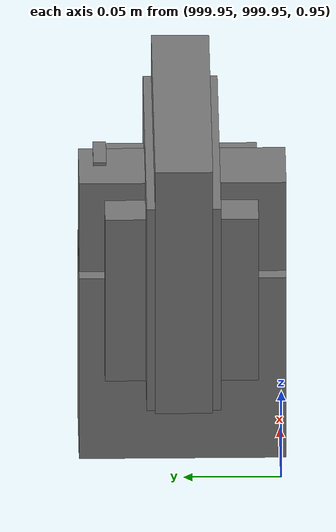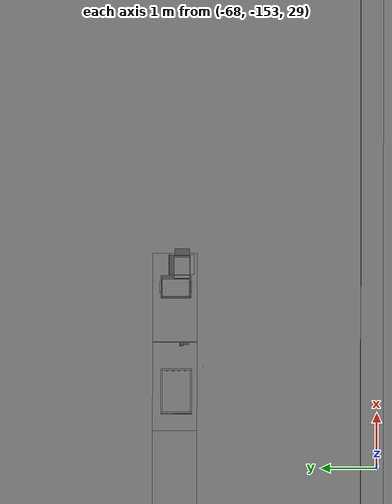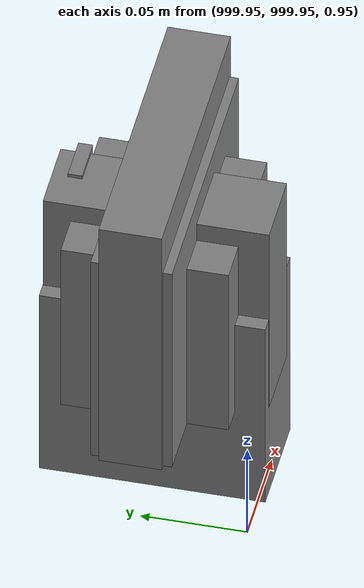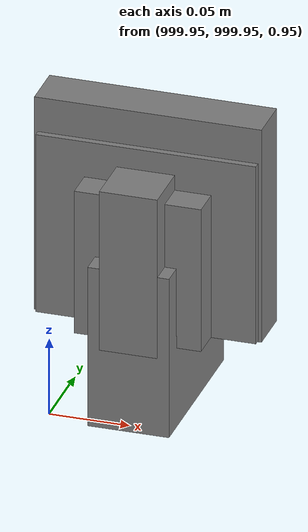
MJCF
<mujoco>
    <option gravity="0.000000000 0.000000000 -9.810000420" timestep="0.0049999999" integrator="implicitfast" density="1.225" viscosity="1.8000001e-05" noslip_iterations="10" iterations="100" sdf_iterations="50">
        <flag multiccd="disable"/>
    </option>
    <size memory="1000M"/>
    <compiler coordinate="local"/>
    <worldbody>
        <light cutoff="30" pos="0 1 1" dir="0 -1 -2"/>
        <light cutoff="30" pos="0 -1 1" dir="0 1 -2"/>
        <body pos="-64.866622925 -149.383972168 30.183746338" euler="89.999984741 89.999946594 0.000000000" name="openloong_gripper_2f85_fix_base_usda_bluebox_01">
            <geom contype="1" conaffinity="1" density="1000" type="box" material="" rgba="0.500000000 0.500000000 0.500000000 1.000000000" solimp="0.899999976 0.949999988 0.001000000" friction="1.000000000 0.005000000 0.000100000" solref="0.020000000 1.000000000" margin="0" condim="3" group="0" pos="0.276580811 0.187225342 0.000068665" quat="0.707106948 0.000077471 0.707106352 0.000077486" size="0.100000001 0.057999998 0.010000000" name="openloong_gripper_2f85_fix_base_usda_geom_80384A35_4019_4FED_8C85_94B8D4554A7A"/>
            <geom contype="1" conaffinity="1" density="1000" type="box" material="" rgba="0.500000000 0.500000000 0.500000000 1.000000000" solimp="0.899999976 0.949999988 0.001000000" friction="1.000000000 0.005000000 0.000100000" solref="0.020000000 1.000000000" margin="0" condim="3" group="0" pos="0.000000000 0.002883911 0.000000000" quat="0.999999881 0.000000000 0.000000000 0.000000000" size="0.254000008 0.003000000 0.172000006" name="openloong_gripper_2f85_fix_base_usda_geom_752DB6E7_4562_4053_A8FE_C75DFC7ABF43"/>
            <geom contype="1" conaffinity="1" density="1000" type="box" material="" rgba="0.500000000 0.500000000 0.500000000 1.000000000" solimp="0.899999976 0.949999988 0.001000000" friction="1.000000000 0.005000000 0.000100000" solref="0.020000000 1.000000000" margin="0" condim="3" group="0" pos="0.000000000 0.124874115 0.173484802" quat="0.999796331 0.020176515 -0.000000015 0.000000030" size="0.259999990 0.119999997 0.007000000" name="openloong_gripper_2f85_fix_base_usda_geom_8A5AAC12_DF4A_47E0_8FFE_6E87B21C8400"/>
            <geom contype="1" conaffinity="1" density="1000" type="box" material="" rgba="0.500000000 0.500000000 0.500000000 1.000000000" solimp="0.899999976 0.949999988 0.001000000" friction="1.000000000 0.005000000 0.000100000" solref="0.020000000 1.000000000" margin="0" condim="3" group="0" pos="0.000000000 0.124874115 -0.173469543" quat="0.999796331 -0.020176545 -0.000000015 0.000000000" size="0.259999990 0.119999997 0.007000000" name="openloong_gripper_2f85_fix_base_usda_geom_9E7BB142_412A_4DB5_A39E_76B78755CA84"/>
            <geom contype="1" conaffinity="1" density="1000" type="box" material="" rgba="0.500000000 0.500000000 0.500000000 1.000000000" solimp="0.899999976 0.949999988 0.001000000" friction="1.000000000 0.005000000 0.000100000" solref="0.020000000 1.000000000" margin="0" condim="3" group="0" pos="0.000000000 0.214008331 0.188980103" quat="0.999912977 0.013176724 0.000000015 0.000000000" size="0.259999990 0.029999999 0.012500000" name="openloong_gripper_2f85_fix_base_usda_geom_DA705AB1_8558_45E5_9BF2_659B4C8E0E32"/>
            <geom contype="1" conaffinity="1" density="1000" type="box" material="" rgba="0.500000000 0.500000000 0.500000000 1.000000000" solimp="0.899999976 0.949999988 0.001000000" friction="1.000000000 0.005000000 0.000100000" solref="0.020000000 1.000000000" margin="0" condim="3" group="0" pos="-0.258361816 0.125289917 0.001876831" quat="0.702796936 -0.020792112 0.710783124 0.020769298" size="0.189999998 0.119999997 0.009000000" name="openloong_gripper_2f85_fix_base_usda_geom_6F66384E_21B0_47B4_B7BD_8A53824C7E45"/>
            <geom contype="1" conaffinity="1" density="1000" type="box" material="" rgba="0.500000000 0.500000000 0.500000000 1.000000000" solimp="0.899999976 0.949999988 0.001000000" friction="1.000000000 0.005000000 0.000100000" solref="0.020000000 1.000000000" margin="0" condim="3" group="0" pos="0.000000000 0.214008331 -0.188980103" quat="0.999912977 -0.013176769 0.000000030 0.000000015" size="0.259999990 0.029999999 0.012500000" name="openloong_gripper_2f85_fix_base_usda_geom_CE9FB3EC_8061_42D5_86C7_692508AB3677"/>
            <geom contype="1" conaffinity="1" density="1000" type="box" material="" rgba="0.500000000 0.500000000 0.500000000 1.000000000" solimp="0.899999976 0.949999988 0.001000000" friction="1.000000000 0.005000000 0.000100000" solref="0.020000000 1.000000000" margin="0" condim="3" group="0" pos="-0.276611328 0.187225342 0.000068665" quat="0.707106650 0.000077441 0.707106709 0.000077456" size="0.100000001 0.057999998 0.010000000" name="openloong_gripper_2f85_fix_base_usda_geom_E77C6F80_6E6D_45DD_86EE_701D32CB6A1D"/>
            <geom contype="1" conaffinity="1" density="1000" type="box" material="" rgba="0.500000000 0.500000000 0.500000000 1.000000000" solimp="0.899999976 0.949999988 0.001000000" friction="1.000000000 0.005000000 0.000100000" solref="0.020000000 1.000000000" margin="0" condim="3" group="0" pos="0.258331299 0.125289917 0.001876831" quat="0.702851415 0.018856421 0.710823774 -0.019329369" size="0.189999998 0.119999997 0.009000000" name="openloong_gripper_2f85_fix_base_usda_geom_74E525FF_92ED_4BA4_82D8_B7550DAFF777"/>
            <freejoint name="openloong_gripper_2f85_fix_base_usda_bluebox_01_joint"/>
            <site size="0.005000000 0.005000000 0.005000000" rgba="0.500000000 0.500000000 0.500000000 1.000000000" pos="0.000000000 0.000000000 0.000000000" quat="0.999961913 0.008726534 0.000000000 0.000000000" group="0" type="sphere" name="openloong_gripper_2f85_fix_base_usda_bluebox_01site"/>
        </body>
        <body pos="-64.496299744 -149.491867065 30.235729218" euler="0.000000000 0.000000000 89.999946594" name="openloong_gripper_2f85_fix_base_usda_cardboardbox_01">
            <geom contype="1" conaffinity="1" density="1000" type="box" material="" rgba="0.500000000 0.500000000 0.500000000 1.000000000" solimp="0.899999976 0.949999988 0.001000000" friction="1.000000000 0.005000000 0.000100000" solref="0.020000000 1.000000000" margin="0" condim="3" group="0" pos="-0.003166199 -0.004086494 0.005052090" quat="1.000000000 0.000000000 0.000000000 0.000000000" size="0.142499998 0.177500010 0.005000000" name="openloong_gripper_2f85_fix_base_usda_geom_245DCF5A_6BD6_435C_AD8F_DC4B82B22434"/>
            <geom contype="1" conaffinity="1" density="1000" type="box" material="" rgba="0.500000000 0.500000000 0.500000000 1.000000000" solimp="0.899999976 0.949999988 0.001000000" friction="1.000000000 0.005000000 0.000100000" solref="0.020000000 1.000000000" margin="0" condim="3" group="0" pos="-0.003166199 0.170316696 0.150570869" quat="1.000000000 0.000000000 0.000000000 0.000000000" size="0.142499998 0.005000000 0.149999991" name="openloong_gripper_2f85_fix_base_usda_geom_87BA6CC3_D4AA_4267_A007_D67D568D1036"/>
            <geom contype="1" conaffinity="1" density="1000" type="box" material="" rgba="0.500000000 0.500000000 0.500000000 1.000000000" solimp="0.899999976 0.949999988 0.001000000" friction="1.000000000 0.005000000 0.000100000" solref="0.020000000 1.000000000" margin="0" condim="3" group="0" pos="-0.147399902 -0.005307198 0.150570869" quat="1.000000000 0.000000000 0.000000000 0.000000000" size="0.005000000 0.177500010 0.149999991" name="openloong_gripper_2f85_fix_base_usda_geom_2B7093E0_8BF9_4D79_99B6_11F261FA0998"/>
            <geom contype="1" conaffinity="1" density="1000" type="box" material="" rgba="0.500000000 0.500000000 0.500000000 1.000000000" solimp="0.899999976 0.949999988 0.001000000" friction="1.000000000 0.005000000 0.000100000" solref="0.020000000 1.000000000" margin="0" condim="3" group="0" pos="0.140275955 -0.005307198 0.150570869" quat="1.000000000 0.000000000 0.000000000 0.000000000" size="0.005000000 0.177500010 0.149999991" name="openloong_gripper_2f85_fix_base_usda_geom_51371E81_C24D_49F1_8242_1F774A8C60DE"/>
            <geom contype="1" conaffinity="1" density="1000" type="box" material="" rgba="0.500000000 0.500000000 0.500000000 1.000000000" solimp="0.899999976 0.949999988 0.001000000" friction="1.000000000 0.005000000 0.000100000" solref="0.020000000 1.000000000" margin="0" condim="3" group="0" pos="-0.003166199 -0.181550980 0.150570869" quat="1.000000000 0.000000000 0.000000000 0.000000000" size="0.142499998 0.005000000 0.149999991" name="openloong_gripper_2f85_fix_base_usda_geom_A7F0A3D7_62EB_4607_BEA8_C133712FACD7"/>
            <freejoint name="openloong_gripper_2f85_fix_base_usda_cardboardbox_01_joint"/>
            <site size="0.005000000 0.005000000 0.005000000" rgba="0.500000000 0.500000000 0.500000000 1.000000000" pos="0.000000000 0.000000000 0.000000000" quat="0.999961913 0.008726535 0.000000000 0.000000000" group="0" type="sphere" name="openloong_gripper_2f85_fix_base_usda_site_35B2D256_62AA_4634_AE7A_1C763442094C"/>
            <body pos="0.139160156 -0.004048347 0.301930904" euler="-179.999954224 49.383502960 179.999954224" name="openloong_gripper_2f85_fix_base_usda_A1_006">
                <geom contype="1" conaffinity="1" density="1000" type="box" material="" rgba="0.500000000 0.500000000 0.500000000 1.000000000" solimp="0.899999976 0.949999988 0.001000000" friction="1.000000000 0.005000000 0.000100000" solref="0.020000000 1.000000000" margin="0" condim="3" group="0" pos="-0.071587563 0.000009537 0.001745224" quat="0.999999881 0.000000000 0.000000000 0.000000000" size="0.071249999 0.179999992 0.002500000" name="openloong_gripper_2f85_fix_base_usda_geom_FB48A7EC_C53B_463B_895D_A15AAAFD8F8A"/>
                <joint armature="0" stiffness="0.07" damping="0.0099999998" axis="0.000000 1.000000 0.000000" type="hinge" name="openloong_gripper_2f85_fix_base_usda_A1_006"/>
            </body>
            <body pos="-0.145902634 -0.004086494 0.301938057" euler="-180.000000000 -60.000011444 -180.000000000" name="openloong_gripper_2f85_fix_base_usda_A2_006">
                <geom contype="1" conaffinity="1" density="1000" type="box" material="" rgba="0.500000000 0.500000000 0.500000000 1.000000000" solimp="0.899999976 0.949999988 0.001000000" friction="1.000000000 0.005000000 0.000100000" solref="0.020000000 1.000000000" margin="0" condim="3" group="0" pos="0.071268082 0.000009537 0.002717972" quat="0.000002921 0.000000000 -0.000000030 0.999999881" size="0.071249999 0.179999992 0.002500000" name="openloong_gripper_2f85_fix_base_usda_geom_10BDD270_9114_4DC4_A9DF_A3AF21B8F798"/>
                <joint armature="0" stiffness="0.07" damping="0.0099999998" axis="0.000000 1.000000 0.000000" type="hinge" name="openloong_gripper_2f85_fix_base_usda_A2_006"/>
            </body>
            <body pos="-0.003385544 0.175991058 0.301930904" euler="-125.858116150 -0.000004561 0.000002331" name="openloong_gripper_2f85_fix_base_usda_B2_006">
                <geom contype="1" conaffinity="1" density="1000" type="box" material="" rgba="0.500000000 0.500000000 0.500000000 1.000000000" solimp="0.899999976 0.949999988 0.001000000" friction="1.000000000 0.005000000 0.000100000" solref="0.020000000 1.000000000" margin="0" condim="3" group="0" pos="0.000009537 -0.070939064 -0.002470016" quat="0.999614120 0.027776197 -0.000000015 0.000000030" size="0.137500003 0.064999998 0.005000000" name="openloong_gripper_2f85_fix_base_usda_geom_04EFBF51_62F1_4C61_8E7F_E6A1C3A34897"/>
                <joint armature="0" stiffness="0.07" damping="0.0099999998" axis="1.000000 0.000000 0.000000" type="hinge" name="openloong_gripper_2f85_fix_base_usda_B2_006"/>
            </body>
            <body pos="-0.003385544 -0.184140205 0.301938057" euler="147.805557251 0.000000000 0.000000000" name="openloong_gripper_2f85_fix_base_usda_B1_006">
                <geom contype="1" conaffinity="1" density="1000" type="box" material="" rgba="0.500000000 0.500000000 0.500000000 1.000000000" solimp="0.899999976 0.949999988 0.001000000" friction="1.000000000 0.005000000 0.000100000" solref="0.020000000 1.000000000" margin="0" condim="3" group="0" pos="-0.000028610 0.070202351 -0.002703667" quat="0.999614179 -0.027776167 0.000000000 0.000000000" size="0.137500003 0.064999998 0.005000000" name="openloong_gripper_2f85_fix_base_usda_geom_4A1EBD86_D201_4A7C_8EF0_4E16D7689C7D"/>
                <joint armature="0" stiffness="0.07" damping="0.0099999998" axis="1.000000 0.000000 0.000000" type="hinge" name="openloong_gripper_2f85_fix_base_usda_B1_006"/>
            </body>
        </body>
        <body pos="-65.882858276 -149.481979370 30.229999542" euler="-64.487716675 0.000000000 0.000000000" name="openloong_gripper_2f85_fix_base_usda_Barcode">
            <geom contype="1" conaffinity="1" density="1000" type="box" material="" rgba="0.500000000 0.500000000 0.500000000 1.000000000" solimp="0.899999976 0.949999988 0.001000000" friction="1.000000000 0.005000000 0.000100000" solref="0.020000000 1.000000000" margin="0" condim="3" group="0" pos="0.000000000 0.013038635 0.001419067" quat="0.000000000 0.000000000 0.000000000 1.000000119" size="0.034000002 0.010000000 0.017999999" name="openloong_gripper_2f85_fix_base_usda_geom_A3C03E60_02F5_4F09_9D6B_0439B8BF4BE5"/>
            <geom contype="1" conaffinity="1" density="1000" type="box" material="" rgba="0.500000000 0.500000000 0.500000000 1.000000000" solimp="0.899999976 0.949999988 0.001000000" friction="1.000000000 0.005000000 0.000100000" solref="0.020000000 1.000000000" margin="0" condim="3" group="0" pos="0.000000000 -0.035301208 -0.007095337" quat="0.000000000 0.000000000 -0.043619365 0.999048233" size="0.028999999 0.010000000 0.020000000" name="openloong_gripper_2f85_fix_base_usda_geom_1C7D5EC2_24E5_46B3_B7CC_1A3FF3D018FF"/>
            <geom contype="1" conaffinity="1" density="1000" type="box" material="" rgba="0.500000000 0.500000000 0.500000000 1.000000000" solimp="0.899999976 0.949999988 0.001000000" friction="1.000000000 0.005000000 0.000100000" solref="0.020000000 1.000000000" margin="0" condim="3" group="0" pos="0.000000000 -0.043411255 -0.011749268" quat="0.922262907 0.386563420 0.000000000 0.000000000" size="0.026000001 0.010000000 0.020000000" name="openloong_gripper_2f85_fix_base_usda_geom_18C203F5_1E01_49A1_AB3A_8F31DDB310E0"/>
            <geom contype="1" conaffinity="1" density="1000" type="box" material="" rgba="0.500000000 0.500000000 0.500000000 1.000000000" solimp="0.899999976 0.949999988 0.001000000" friction="1.000000000 0.005000000 0.000100000" solref="0.020000000 1.000000000" margin="0" condim="3" group="0" pos="0.000000000 -0.016967773 -0.031860352" quat="0.000000000 0.000000000 0.000000000 1.000000119" size="0.008000000 0.010000000 0.013000000" name="openloong_gripper_2f85_fix_base_usda_geom_42128904_6CD2_4336_9DF6_DCAAB93B68CB"/>
            <geom contype="1" conaffinity="1" density="1000" type="box" material="" rgba="0.500000000 0.500000000 0.500000000 1.000000000" solimp="0.899999976 0.949999988 0.001000000" friction="1.000000000 0.005000000 0.000100000" solref="0.020000000 1.000000000" margin="0" condim="3" group="0" pos="0.000000000 -0.001869202 0.000312805" quat="0.953716993 0.300705761 0.000000000 0.000000000" size="0.032000002 0.010000000 0.018999999" name="openloong_gripper_2f85_fix_base_usda_geom_B5D6A3A7_91E0_466C_B87F_C62E68D0978B"/>
            <geom contype="1" conaffinity="1" density="1000" type="box" material="" rgba="0.500000000 0.500000000 0.500000000 1.000000000" solimp="0.899999976 0.949999988 0.001000000" friction="1.000000000 0.005000000 0.000100000" solref="0.020000000 1.000000000" margin="0" condim="3" group="0" pos="0.000000000 -0.019531250 -0.003173828" quat="0.953716993 0.300705761 0.000000000 0.000000000" size="0.030999999 0.010000000 0.020000000" name="openloong_gripper_2f85_fix_base_usda_geom_86FC3883_25F9_4B58_A57F_B831B3F711EF"/>
            <geom contype="1" conaffinity="1" density="1000" type="box" material="" rgba="0.500000000 0.500000000 0.500000000 1.000000000" solimp="0.899999976 0.949999988 0.001000000" friction="1.000000000 0.005000000 0.000100000" solref="0.020000000 1.000000000" margin="0" condim="3" group="0" pos="0.000000000 -0.035301208 -0.007095337" quat="0.953716993 0.300705761 0.000000000 0.000000000" size="0.028999999 0.010000000 0.020000000" name="openloong_gripper_2f85_fix_base_usda_geom_5ADB1A47_F5C0_435F_8E87_A19D4FA83797"/>
            <geom contype="1" conaffinity="1" density="1000" type="box" material="" rgba="0.500000000 0.500000000 0.500000000 1.000000000" solimp="0.899999976 0.949999988 0.001000000" friction="1.000000000 0.005000000 0.000100000" solref="0.020000000 1.000000000" margin="0" condim="3" group="0" pos="0.000000000 -0.042617798 -0.071121216" quat="0.000000000 0.000000000 0.000000000 1.000000119" size="0.013000000 0.021000000 0.059999999" name="openloong_gripper_2f85_fix_base_usda_geom_B2A09FD6_2D46_4428_B271_A6956C79F058"/>
            <freejoint name="openloong_gripper_2f85_fix_base_usda_Barcode_joint"/>
            <site size="0.005000000 0.005000000 0.005000000" rgba="0.500000000 0.500000000 0.500000000 1.000000000" pos="0.000000000 0.000000000 0.000000000" quat="1.000000000 0.000000000 0.000000000 0.000000000" group="0" type="sphere" name="openloong_gripper_2f85_fix_base_usda_Barcode_site"/>
        </body>
        <body pos="-66.745018005 -149.392349243 30.184000015" euler="0.000000000 0.000000000 89.999946594" name="[22332185149348]_Basket_01">
            <geom contype="1" conaffinity="1" density="1000" type="box" material="" rgba="0.500000000 0.500000000 0.500000000 1.000000000" solimp="0.899999976 0.949999988 0.001000000" friction="1.000000000 0.005000000 0.000100000" solref="0.020000000 1.000000000" margin="0" condim="3" group="0" pos="-0.052425385 0.389207840 0.089787483" quat="0.707107008 0.000000000 0.000000000 0.707106411" size="0.014249999 0.014249999 0.059999999" name="[22332185149348]_geom_EF729F48_1D92_4800_8EDF_D75E693398EB"/>
            <geom contype="1" conaffinity="1" density="1000" type="box" material="" rgba="0.500000000 0.500000000 0.500000000 1.000000000" solimp="0.899999976 0.949999988 0.001000000" friction="1.000000000 0.005000000 0.000100000" solref="0.020000000 1.000000000" margin="0" condim="3" group="0" pos="0.264015198 -0.133043289 0.089787483" quat="0.707107008 0.000000000 0.000000000 0.707106411" size="0.014249999 0.014249999 0.059999999" name="[22332185149348]_geom_4081A935_D300_40CA_A7C3_65DF29742CC5"/>
            <geom contype="1" conaffinity="1" density="1000" type="box" material="" rgba="0.500000000 0.500000000 0.500000000 1.000000000" solimp="0.899999976 0.949999988 0.001000000" friction="1.000000000 0.005000000 0.000100000" solref="0.020000000 1.000000000" margin="0" condim="3" group="0" pos="-0.264015198 -0.265548706 0.089793205" quat="0.707107008 0.000000000 0.000000000 0.707106411" size="0.014249999 0.014249999 0.059999999" name="[22332185149348]_geom_A2A4668C_C66F_4439_A578_5C89B222921A"/>
            <geom contype="1" conaffinity="1" density="1000" type="box" material="" rgba="0.500000000 0.500000000 0.500000000 1.000000000" solimp="0.899999976 0.949999988 0.001000000" friction="1.000000000 0.005000000 0.000100000" solref="0.020000000 1.000000000" margin="0" condim="3" group="0" pos="-0.160263062 -0.389322281 0.089793205" quat="0.707107008 0.000000000 0.000000000 0.707106411" size="0.014249999 0.014249999 0.059999999" name="[22332185149348]_geom_07CB228C_D488_48A1_9B14_3D66D80D3AB0"/>
            <geom contype="1" conaffinity="1" density="1000" type="box" material="" rgba="0.500000000 0.500000000 0.500000000 1.000000000" solimp="0.899999976 0.949999988 0.001000000" friction="1.000000000 0.005000000 0.000100000" solref="0.020000000 1.000000000" margin="0" condim="3" group="0" pos="0.162265778 -0.389322281 0.089787483" quat="0.707107008 0.000000000 0.000000000 0.707106411" size="0.014249999 0.014249999 0.059999999" name="[22332185149348]_geom_710104E0_EA31_4563_9221_AED5EDE64D8F"/>
            <geom contype="1" conaffinity="1" density="1000" type="box" material="" rgba="0.500000000 0.500000000 0.500000000 1.000000000" solimp="0.899999976 0.949999988 0.001000000" friction="1.000000000 0.005000000 0.000100000" solref="0.020000000 1.000000000" margin="0" condim="3" group="0" pos="0.264015198 0.389207840 0.089787483" quat="0.707107008 0.000000000 0.000000000 0.707106411" size="0.014249999 0.014249999 0.059999999" name="[22332185149348]_geom_CA441CBC_4096_483D_BC74_CAA24771CDB6"/>
            <geom contype="1" conaffinity="1" density="1000" type="box" material="" rgba="0.500000000 0.500000000 0.500000000 1.000000000" solimp="0.899999976 0.949999988 0.001000000" friction="1.000000000 0.005000000 0.000100000" solref="0.020000000 1.000000000" margin="0" condim="3" group="0" pos="-0.264015198 -0.133043289 0.089793205" quat="0.707107008 0.000000000 0.000000000 0.707106411" size="0.014249999 0.014249999 0.059999999" name="[22332185149348]_geom_A1A89106_BC10_4871_BD2E_1CE5973C96E8"/>
            <geom contype="1" conaffinity="1" density="1000" type="box" material="" rgba="0.500000000 0.500000000 0.500000000 1.000000000" solimp="0.899999976 0.949999988 0.001000000" friction="1.000000000 0.005000000 0.000100000" solref="0.020000000 1.000000000" margin="0" condim="3" group="0" pos="-0.264026642 0.269256592 0.089793205" quat="0.707107008 0.000000000 0.000000000 0.707106411" size="0.014249999 0.014249999 0.059999999" name="[22332185149348]_geom_A80DF48B_9B34_40E8_8E50_402AFA03C5C5"/>
            <geom contype="1" conaffinity="1" density="1000" type="box" material="" rgba="0.500000000 0.500000000 0.500000000 1.000000000" solimp="0.899999976 0.949999988 0.001000000" friction="1.000000000 0.005000000 0.000100000" solref="0.020000000 1.000000000" margin="0" condim="3" group="0" pos="0.054462433 0.389207840 0.089787483" quat="0.707107008 0.000000000 0.000000000 0.707106411" size="0.014249999 0.014249999 0.059999999" name="[22332185149348]_geom_6D9BBB10_C51A_4E47_82DF_3767BEE036CC"/>
            <geom contype="1" conaffinity="1" density="1000" type="box" material="" rgba="0.500000000 0.500000000 0.500000000 1.000000000" solimp="0.899999976 0.949999988 0.001000000" friction="1.000000000 0.005000000 0.000100000" solref="0.020000000 1.000000000" margin="0" condim="3" group="0" pos="0.054462433 -0.389322281 0.089787483" quat="0.707107008 0.000000000 0.000000000 0.707106411" size="0.014249999 0.014249999 0.059999999" name="[22332185149348]_geom_4999F568_D8D8_4DBA_BF28_662C6D404BA4"/>
            <geom contype="1" conaffinity="1" density="1000" type="box" material="" rgba="0.500000000 0.500000000 0.500000000 1.000000000" solimp="0.899999976 0.949999988 0.001000000" friction="1.000000000 0.005000000 0.000100000" solref="0.020000000 1.000000000" margin="0" condim="3" group="0" pos="0.264015198 0.269256592 0.089793205" quat="0.707107008 0.000000000 0.000000000 0.707106411" size="0.014249999 0.014249999 0.059999999" name="[22332185149348]_geom_FFE0985D_248B_419C_9E19_C8D940A1EB33"/>
            <geom contype="1" conaffinity="1" density="1000" type="box" material="" rgba="0.500000000 0.500000000 0.500000000 1.000000000" solimp="0.899999976 0.949999988 0.001000000" friction="1.000000000 0.005000000 0.000100000" solref="0.020000000 1.000000000" margin="0" condim="3" group="0" pos="0.264015198 -0.389322281 0.089787483" quat="0.707107008 0.000000000 0.000000000 0.707106411" size="0.014249999 0.014249999 0.059999999" name="[22332185149348]_geom_B1E8E1D4_AC05_421B_A8C0_3F091E964845"/>
            <geom contype="1" conaffinity="1" density="1000" type="box" material="" rgba="0.500000000 0.500000000 0.500000000 1.000000000" solimp="0.899999976 0.949999988 0.001000000" friction="1.000000000 0.005000000 0.000100000" solref="0.020000000 1.000000000" margin="0" condim="3" group="0" pos="0.000000000 0.000000000 0.015998840" quat="0.707107008 0.000000000 0.000000000 0.707106411" size="0.403499991 0.279000014 0.015750000" name="[22332185149348]_geom_268FBC42_21E9_4E28_97A3_4535AA0BF287"/>
            <geom contype="1" conaffinity="1" density="1000" type="box" material="" rgba="0.500000000 0.500000000 0.500000000 1.000000000" solimp="0.899999976 0.949999988 0.001000000" friction="1.000000000 0.005000000 0.000100000" solref="0.020000000 1.000000000" margin="0" condim="3" group="0" pos="0.000000000 -0.389476776 0.163619041" quat="0.707107008 0.000000000 0.000000000 0.707106411" size="0.015000000 0.277500004 0.015750000" name="[22332185149348]_geom_9A630709_6F40_4405_8C68_0D999B6EC834"/>
            <geom contype="1" conaffinity="1" density="1000" type="box" material="" rgba="0.500000000 0.500000000 0.500000000 1.000000000" solimp="0.899999976 0.949999988 0.001000000" friction="1.000000000 0.005000000 0.000100000" solref="0.020000000 1.000000000" margin="0" condim="3" group="0" pos="0.162265778 0.389207840 0.089787483" quat="0.707107008 0.000000000 0.000000000 0.707106411" size="0.014249999 0.014249999 0.059999999" name="[22332185149348]_geom_45FBD72F_7542_48CA_A4B7_4A81EC3C5075"/>
            <geom contype="1" conaffinity="1" density="1000" type="box" material="" rgba="0.500000000 0.500000000 0.500000000 1.000000000" solimp="0.899999976 0.949999988 0.001000000" friction="1.000000000 0.005000000 0.000100000" solref="0.020000000 1.000000000" margin="0" condim="3" group="0" pos="0.000000000 0.389471054 0.163619041" quat="0.707107008 0.000000000 0.000000000 0.707106411" size="0.015000000 0.277500004 0.015750000" name="[22332185149348]_geom_E7CFD9E9_89CB_4C7C_8BBD_DE3D0852E68A"/>
            <geom contype="1" conaffinity="1" density="1000" type="box" material="" rgba="0.500000000 0.500000000 0.500000000 1.000000000" solimp="0.899999976 0.949999988 0.001000000" friction="1.000000000 0.005000000 0.000100000" solref="0.020000000 1.000000000" margin="0" condim="3" group="0" pos="-0.263511658 0.000000000 0.163619041" quat="0.707107008 0.000000000 0.000000000 0.707106411" size="0.403499991 0.015000000 0.015750000" name="[22332185149348]_geom_4CF594C8_D007_462C_A373_E2C4D18AD4CB"/>
            <geom contype="1" conaffinity="1" density="1000" type="box" material="" rgba="0.500000000 0.500000000 0.500000000 1.000000000" solimp="0.899999976 0.949999988 0.001000000" friction="1.000000000 0.005000000 0.000100000" solref="0.020000000 1.000000000" margin="0" condim="3" group="0" pos="-0.264015198 0.141334534 0.089793205" quat="0.707107008 0.000000000 0.000000000 0.707106411" size="0.014249999 0.014249999 0.059999999" name="[22332185149348]_geom_FFD06085_F8B2_4146_A851_1588FF4F8819"/>
            <geom contype="1" conaffinity="1" density="1000" type="box" material="" rgba="0.500000000 0.500000000 0.500000000 1.000000000" solimp="0.899999976 0.949999988 0.001000000" friction="1.000000000 0.005000000 0.000100000" solref="0.020000000 1.000000000" margin="0" condim="3" group="0" pos="0.264015198 -0.265548706 0.089787483" quat="0.707107008 0.000000000 0.000000000 0.707106411" size="0.014249999 0.014249999 0.059999999" name="[22332185149348]_geom_FB6822AC_9F27_41EB_A15E_BC152D1E44E1"/>
            <geom contype="1" conaffinity="1" density="1000" type="box" material="" rgba="0.500000000 0.500000000 0.500000000 1.000000000" solimp="0.899999976 0.949999988 0.001000000" friction="1.000000000 0.005000000 0.000100000" solref="0.020000000 1.000000000" margin="0" condim="3" group="0" pos="-0.160263062 0.389207840 0.089787483" quat="0.707107008 0.000000000 0.000000000 0.707106411" size="0.014249999 0.014249999 0.059999999" name="[22332185149348]_geom_E0595B05_CE5C_4AA7_BC5C_EB96BF4575B5"/>
            <geom contype="1" conaffinity="1" density="1000" type="box" material="" rgba="0.500000000 0.500000000 0.500000000 1.000000000" solimp="0.899999976 0.949999988 0.001000000" friction="1.000000000 0.005000000 0.000100000" solref="0.020000000 1.000000000" margin="0" condim="3" group="0" pos="-0.052425385 -0.389322281 0.089787483" quat="0.707107008 0.000000000 0.000000000 0.707106411" size="0.014249999 0.014249999 0.059999999" name="[22332185149348]_geom_6FFC30EA_147C_4510_BBB0_0F5E1CAAF0A4"/>
            <geom contype="1" conaffinity="1" density="1000" type="box" material="" rgba="0.500000000 0.500000000 0.500000000 1.000000000" solimp="0.899999976 0.949999988 0.001000000" friction="1.000000000 0.005000000 0.000100000" solref="0.020000000 1.000000000" margin="0" condim="3" group="0" pos="-0.264026642 -0.389322281 0.089793205" quat="0.707107008 0.000000000 0.000000000 0.707106411" size="0.014249999 0.014249999 0.059999999" name="[22332185149348]_geom_FFA5374C_ADD4_453E_AA6D_3EC11C2E1729"/>
            <geom contype="1" conaffinity="1" density="1000" type="box" material="" rgba="0.500000000 0.500000000 0.500000000 1.000000000" solimp="0.899999976 0.949999988 0.001000000" friction="1.000000000 0.005000000 0.000100000" solref="0.020000000 1.000000000" margin="0" condim="3" group="0" pos="0.264015198 0.141334534 0.089787483" quat="0.707107008 0.000000000 0.000000000 0.707106411" size="0.014249999 0.014249999 0.059999999" name="[22332185149348]_geom_C2786326_E3BD_418D_8817_FE2A7B55723D"/>
            <geom contype="1" conaffinity="1" density="1000" type="box" material="" rgba="0.500000000 0.500000000 0.500000000 1.000000000" solimp="0.899999976 0.949999988 0.001000000" friction="1.000000000 0.005000000 0.000100000" solref="0.020000000 1.000000000" margin="0" condim="3" group="0" pos="-0.264015198 0.389207840 0.089793205" quat="0.707107008 0.000000000 0.000000000 0.707106411" size="0.014249999 0.014249999 0.059999999" name="[22332185149348]_geom_F568055E_C414_4498_A1CF_28C7958DF19C"/>
            <geom contype="1" conaffinity="1" density="1000" type="box" material="" rgba="0.500000000 0.500000000 0.500000000 1.000000000" solimp="0.899999976 0.949999988 0.001000000" friction="1.000000000 0.005000000 0.000100000" solref="0.020000000 1.000000000" margin="0" condim="3" group="0" pos="0.264015198 0.004480362 0.089787483" quat="0.707107008 0.000000000 0.000000000 0.707106411" size="0.014249999 0.014249999 0.059999999" name="[22332185149348]_geom_20E0E382_69F7_4ED6_A24F_A99A0CCD0E88"/>
            <geom contype="1" conaffinity="1" density="1000" type="box" material="" rgba="0.500000000 0.500000000 0.500000000 1.000000000" solimp="0.899999976 0.949999988 0.001000000" friction="1.000000000 0.005000000 0.000100000" solref="0.020000000 1.000000000" margin="0" condim="3" group="0" pos="0.263694763 -0.000011444 0.163619041" quat="0.707107008 0.000000000 0.000000000 0.707106411" size="0.403499991 0.015000000 0.015750000" name="[22332185149348]_geom_FC2A20B5_8938_46DD_A523_5206DCEB81F6"/>
            <geom contype="1" conaffinity="1" density="1000" type="box" material="" rgba="0.500000000 0.500000000 0.500000000 1.000000000" solimp="0.899999976 0.949999988 0.001000000" friction="1.000000000 0.005000000 0.000100000" solref="0.020000000 1.000000000" margin="0" condim="3" group="0" pos="-0.264015198 0.004480362 0.089793205" quat="0.707107008 0.000000000 0.000000000 0.707106411" size="0.014249999 0.014249999 0.059999999" name="[22332185149348]_geom_9DF0C31F_92FF_4C15_98F7_F0B9FEBB5854"/>
            <freejoint name="[22332185149348]_joint_D4F50C55_C396_477D_A31B_53C70A4E3F44"/>
        </body>
        <body pos="0.000000000 0.000000000 0.000000000" euler="0.000000000 0.000000000 0.000000000" name="Static Objects_Static Objects">
            <geom contype="1" conaffinity="1" density="1000" type="box" material="" rgba="0.500000000 0.500000000 0.500000000 1.000000000" solimp="0.899999976 0.949999988 0.001000000" friction="1.000000000 0.005000000 0.000100000" solref="0.020000000 1.000000000" margin="0" condim="3" group="0" pos="-67.544113159 -149.365814209 29.727830887" quat="0.500000417 0.499999970 0.499999553 0.499999970" size="0.381000012 0.319999993 0.041000001" name="Static Objects_geom_F1E69155_AB85_4EEC_842B_F84B9F8360A6"/>
            <geom contype="1" conaffinity="1" density="1000" type="box" material="" rgba="0.500000000 0.500000000 0.500000000 1.000000000" solimp="0.899999976 0.949999988 0.001000000" friction="1.000000000 0.005000000 0.000100000" solref="0.020000000 1.000000000" margin="0" condim="3" group="0" pos="-68.239501953 -149.365814209 30.086868286" quat="0.500000417 0.499999970 0.499999553 0.499999970" size="0.370999992 0.039500002 0.745000005" name="Static Objects_geom_08C677E8_D8D7_4A70_A0A2_3267D97205CA"/>
            <geom contype="1" conaffinity="1" density="1000" type="box" material="" rgba="0.500000000 0.500000000 0.500000000 1.000000000" solimp="0.899999976 0.949999988 0.001000000" friction="1.000000000 0.005000000 0.000100000" solref="0.020000000 1.000000000" margin="0" condim="3" group="0" pos="-68.239501953 -149.365814209 30.147235870" quat="0.500000417 0.499999970 0.499999553 0.499999970" size="0.400000006 0.022000000 0.800000012" name="Static Objects_geom_A8C5B754_603E_46A2_9AB9_397559D3BC50"/>
            <geom contype="1" conaffinity="1" density="1000" type="box" material="" rgba="0.500000000 0.500000000 0.500000000 1.000000000" solimp="0.899999976 0.949999988 0.001000000" friction="1.000000000 0.005000000 0.000100000" solref="0.020000000 1.000000000" margin="0" condim="3" group="0" pos="-68.934890747 -149.365814209 29.727830887" quat="0.500000417 0.499999970 0.499999553 0.499999970" size="0.381000012 0.319999993 0.041000001" name="Static Objects_geom_8AEB8E35_55D0_4EB8_BC0E_23C28BFA6532"/>
            <geom contype="1" conaffinity="1" density="1000" type="box" material="" rgba="0.500000000 0.500000000 0.500000000 1.000000000" solimp="0.899999976 0.949999988 0.001000000" friction="1.000000000 0.005000000 0.000100000" solref="0.020000000 1.000000000" margin="0" condim="3" group="0" pos="-68.239501953 -149.365814209 29.561563492" quat="0.500000417 0.499999970 0.499999553 0.499999970" size="0.020000000 0.022000000 0.660000026" name="Static Objects_geom_C418024B_7511_4A6C_96B2_0ECAE7E8187D"/>
            <geom contype="1" conaffinity="1" density="1000" type="box" material="" rgba="0.500000000 0.500000000 0.500000000 1.000000000" solimp="0.899999976 0.949999988 0.001000000" friction="1.000000000 0.005000000 0.000100000" solref="0.020000000 1.000000000" margin="0" condim="3" group="0" pos="-65.945671082 -149.365814209 29.727830887" quat="0.500000417 0.499999970 0.499999553 0.499999970" size="0.381000012 0.319999993 0.041000001" name="Static Objects_geom_41A91B7D_B320_4AB7_BA8D_78905D660F97"/>
            <geom contype="1" conaffinity="1" density="1000" type="box" material="" rgba="0.500000000 0.500000000 0.500000000 1.000000000" solimp="0.899999976 0.949999988 0.001000000" friction="1.000000000 0.005000000 0.000100000" solref="0.020000000 1.000000000" margin="0" condim="3" group="0" pos="-66.641059875 -149.365814209 30.086868286" quat="0.500000417 0.499999970 0.499999553 0.499999970" size="0.370999992 0.039500002 0.745000005" name="Static Objects_geom_C82F38D3_E463_404E_912C_8F607344B2C0"/>
            <geom contype="1" conaffinity="1" density="1000" type="box" material="" rgba="0.500000000 0.500000000 0.500000000 1.000000000" solimp="0.899999976 0.949999988 0.001000000" friction="1.000000000 0.005000000 0.000100000" solref="0.020000000 1.000000000" margin="0" condim="3" group="0" pos="-66.641059875 -149.365814209 30.147235870" quat="0.500000417 0.499999970 0.499999553 0.499999970" size="0.400000006 0.022000000 0.800000012" name="Static Objects_geom_0D512C60_2C3C_4967_831E_4E4DE9D575C4"/>
            <geom contype="1" conaffinity="1" density="1000" type="box" material="" rgba="0.500000000 0.500000000 0.500000000 1.000000000" solimp="0.899999976 0.949999988 0.001000000" friction="1.000000000 0.005000000 0.000100000" solref="0.020000000 1.000000000" margin="0" condim="3" group="0" pos="-67.336448669 -149.365814209 29.727830887" quat="0.500000417 0.499999970 0.499999553 0.499999970" size="0.381000012 0.319999993 0.041000001" name="Static Objects_geom_A57BE272_34E5_4073_88AA_B5F23991FB2E"/>
            <geom contype="1" conaffinity="1" density="1000" type="box" material="" rgba="0.500000000 0.500000000 0.500000000 1.000000000" solimp="0.899999976 0.949999988 0.001000000" friction="1.000000000 0.005000000 0.000100000" solref="0.020000000 1.000000000" margin="0" condim="3" group="0" pos="-66.641059875 -149.365814209 29.561563492" quat="0.500000417 0.499999970 0.499999553 0.499999970" size="0.020000000 0.022000000 0.660000026" name="Static Objects_geom_47D42360_7B1A_4828_BE05_52A1DEC36BD5"/>
            <geom contype="1" conaffinity="1" density="1000" type="box" material="" rgba="0.500000000 0.500000000 0.500000000 1.000000000" solimp="0.899999976 0.949999988 0.001000000" friction="1.000000000 0.005000000 0.000100000" solref="0.020000000 1.000000000" margin="0" condim="3" group="0" pos="-64.338577271 -149.365814209 29.727830887" quat="0.500000417 0.499999970 0.499999553 0.499999970" size="0.381000012 0.319999993 0.041000001" name="Static Objects_geom_F3F89EC2_099C_4FE7_B135_3FCB7866A0CB"/>
            <geom contype="1" conaffinity="1" density="1000" type="box" material="" rgba="0.500000000 0.500000000 0.500000000 1.000000000" solimp="0.899999976 0.949999988 0.001000000" friction="1.000000000 0.005000000 0.000100000" solref="0.020000000 1.000000000" margin="0" condim="3" group="0" pos="-65.033966064 -149.365814209 30.086868286" quat="0.500000417 0.499999970 0.499999553 0.499999970" size="0.370999992 0.039500002 0.745000005" name="Static Objects_geom_A1AACD89_9213_4E59_A06D_52375FF505C3"/>
            <geom contype="1" conaffinity="1" density="1000" type="box" material="" rgba="0.500000000 0.500000000 0.500000000 1.000000000" solimp="0.899999976 0.949999988 0.001000000" friction="1.000000000 0.005000000 0.000100000" solref="0.020000000 1.000000000" margin="0" condim="3" group="0" pos="-65.033966064 -149.365814209 30.147235870" quat="0.500000417 0.499999970 0.499999553 0.499999970" size="0.400000006 0.022000000 0.800000012" name="Static Objects_geom_AA22BCBE_FA2B_4B03_895C_5EB480ED43DB"/>
            <geom contype="1" conaffinity="1" density="1000" type="box" material="" rgba="0.500000000 0.500000000 0.500000000 1.000000000" solimp="0.899999976 0.949999988 0.001000000" friction="1.000000000 0.005000000 0.000100000" solref="0.020000000 1.000000000" margin="0" condim="3" group="0" pos="-65.729354858 -149.365814209 29.727830887" quat="0.500000417 0.499999970 0.499999553 0.499999970" size="0.381000012 0.319999993 0.041000001" name="Static Objects_geom_BC7CA814_8AD3_42F4_9A6A_69C369BB98DF"/>
            <geom contype="1" conaffinity="1" density="1000" type="box" material="" rgba="0.500000000 0.500000000 0.500000000 1.000000000" solimp="0.899999976 0.949999988 0.001000000" friction="1.000000000 0.005000000 0.000100000" solref="0.020000000 1.000000000" margin="0" condim="3" group="0" pos="-65.033966064 -149.365814209 29.561563492" quat="0.500000417 0.499999970 0.499999553 0.499999970" size="0.020000000 0.022000000 0.660000026" name="Static Objects_geom_97C5C4A2_93AE_4817_9E1E_03F66667E4F0"/>
            <geom contype="1" conaffinity="1" density="1000" type="box" material="" rgba="0.500000000 0.500000000 0.500000000 1.000000000" solimp="0.899999976 0.949999988 0.001000000" friction="1.000000000 0.005000000 0.000100000" solref="0.020000000 1.000000000" margin="0" condim="3" group="0" pos="-61.754566193 -137.853729248 33.906845093" quat="0.707107067 0.000000000 0.000000000 0.707106471" size="0.759999990 0.759999990 4.500000000" name="Static Objects_geom_153BA20E_A1A2_4822_8AE8_792A47923A8C"/>
            <geom contype="1" conaffinity="1" density="1000" type="box" material="" rgba="0.500000000 0.500000000 0.500000000 1.000000000" solimp="0.899999976 0.949999988 0.001000000" friction="1.000000000 0.005000000 0.000100000" solref="0.020000000 1.000000000" margin="0" condim="3" group="0" pos="-57.511135101 -144.927108765 31.707921982" quat="1.000000000 0.000000000 0.000000000 0.000000000" size="0.200000003 8.000000000 2.299999952" name="Static Objects_geom_903F4B37_63AC_4CEC_B7E6_7E5051684FB5"/>
            <geom contype="1" conaffinity="1" density="1000" type="box" material="" rgba="0.500000000 0.500000000 0.500000000 1.000000000" solimp="0.899999976 0.949999988 0.001000000" friction="1.000000000 0.005000000 0.000100000" solref="0.020000000 1.000000000" margin="0" condim="3" group="0" pos="-80.517646790 -157.574050903 31.688196182" quat="0.707107067 0.000000000 0.000000000 0.707106471" size="0.600000024 0.600000024 2.299999952" name="Static Objects_geom_995BA06E_2030_4091_8972_B0612FD03457"/>
            <geom contype="1" conaffinity="1" density="1000" type="box" material="" rgba="0.500000000 0.500000000 0.500000000 1.000000000" solimp="0.899999976 0.949999988 0.001000000" friction="1.000000000 0.005000000 0.000100000" solref="0.020000000 1.000000000" margin="0" condim="3" group="0" pos="-80.711044312 -147.414932251 31.666158676" quat="1.000000000 0.000000000 0.000000000 0.000000000" size="0.200000003 10.000000000 2.299999952" name="Static Objects_geom_410B6C44_ABA8_4CF2_AE8C_18731E93C6DC"/>
            <geom contype="1" conaffinity="1" density="1000" type="box" material="" rgba="0.500000000 0.500000000 0.500000000 1.000000000" solimp="0.899999976 0.949999988 0.001000000" friction="1.000000000 0.005000000 0.000100000" solref="0.020000000 1.000000000" margin="0" condim="3" group="0" pos="-57.687217712 -137.434692383 31.688196182" quat="0.707107067 0.000000000 0.000000000 0.707106471" size="0.600000024 0.600000024 2.299999952" name="Static Objects_geom_CDA60EA7_5689_47DC_88CD_F95146DF1253"/>
            <geom contype="1" conaffinity="1" density="1000" type="box" material="" rgba="0.500000000 0.500000000 0.500000000 1.000000000" solimp="0.899999976 0.949999988 0.001000000" friction="1.000000000 0.005000000 0.000100000" solref="0.020000000 1.000000000" margin="0" condim="3" group="0" pos="-69.537033081 -140.263229370 31.714921951" quat="0.707107067 0.000000000 0.000000000 0.707106471" size="0.759999990 4.500000000 2.299999952" name="Static Objects_geom_7A8ED2AC_713A_405B_B9DE_985571380E0F"/>
            <geom contype="1" conaffinity="1" density="1000" type="box" material="" rgba="0.500000000 0.500000000 0.500000000 1.000000000" solimp="0.899999976 0.949999988 0.001000000" friction="1.000000000 0.005000000 0.000100000" solref="0.020000000 1.000000000" margin="0" condim="3" group="0" pos="-80.073638916 -137.853713989 33.906845093" quat="0.707107067 0.000000000 0.000000000 0.707106471" size="0.759999990 0.759999990 4.500000000" name="Static Objects_geom_54170F69_9029_4DE3_80F3_3CB60FF82A6F"/>
            <geom contype="1" conaffinity="1" density="1000" type="box" material="" rgba="0.500000000 0.500000000 0.500000000 1.000000000" solimp="0.899999976 0.949999988 0.001000000" friction="1.000000000 0.005000000 0.000100000" solref="0.020000000 1.000000000" margin="0" condim="3" group="0" pos="-73.406707764 -155.734664917 31.707921982" quat="1.000000000 0.000000000 0.000000000 0.000000000" size="0.200000003 3.000000000 2.299999952" name="Static Objects_geom_CDF79D52_72BE_4947_B3F7_97783E4D3226"/>
            <geom contype="1" conaffinity="1" density="1000" type="box" material="" rgba="0.500000000 0.500000000 0.500000000 1.000000000" solimp="0.899999976 0.949999988 0.001000000" friction="1.000000000 0.005000000 0.000100000" solref="0.020000000 1.000000000" margin="0" condim="3" group="0" pos="-68.497543335 -137.448257446 31.707921982" quat="0.707107067 0.000000000 0.000000000 0.707106471" size="0.200000003 14.000000000 2.299999952" name="Static Objects_geom_D69EB616_B241_406E_B217_4A395B8A2E20"/>
            <geom contype="1" conaffinity="1" density="1000" type="cylinder" material="" rgba="0.500000000 0.500000000 0.500000000 1.000000000" solimp="0.899999976 0.949999988 0.001000000" friction="1.000000000 0.005000000 0.000100000" solref="0.020000000 1.000000000" margin="0" condim="3" group="0" pos="-68.868522644 -142.134506226 31.711090088" quat="0.707107067 0.000000000 0.000000000 0.707106471" size="0.509999990 2.299999952 1.000000000" name="Static Objects_geom_B4C24C0A_BD5D_4C48_9F10_35351DD3513C"/>
            <geom contype="1" conaffinity="1" density="1000" type="plane" material="" rgba="0.500000000 0.500000000 0.500000000 1.000000000" solimp="0.899999976 0.949999988 0.001000000" friction="1.000000000 0.005000000 0.000100000" solref="0.020000000 1.000000000" margin="0" condim="3" group="0" pos="-72.873703003 -147.131927490 29.409669876" quat="1.000000000 0.000000000 0.000000000 0.000000000" size="18.000000000 14.000000000 1.000000000" name="Static Objects_geom_1AEB960D_0928_4559_A84F_2CD3262DFBE5"/>
            <geom contype="1" conaffinity="1" density="1000" type="box" material="" rgba="0.500000000 0.500000000 0.500000000 1.000000000" solimp="0.899999976 0.949999988 0.001000000" friction="1.000000000 0.005000000 0.000100000" solref="0.020000000 1.000000000" margin="0" condim="3" group="0" pos="-79.943580627 -157.782272339 31.707921982" quat="0.707107067 0.000000000 0.000000000 0.707106471" size="0.200000003 7.000000000 2.299999952" name="Static Objects_geom_FC15F9A6_B792_492A_8A0B_8EBAB60CEFC8"/>
            <geom contype="1" conaffinity="1" density="1000" type="box" material="" rgba="0.500000000 0.500000000 0.500000000 1.000000000" solimp="0.899999976 0.949999988 0.001000000" friction="1.000000000 0.005000000 0.000100000" solref="0.020000000 1.000000000" margin="0" condim="3" group="0" pos="-65.421028137 -152.903442383 31.707921982" quat="0.707107067 0.000000000 0.000000000 0.707106471" size="0.200000003 7.800000191 2.299999952" name="Static Objects_geom_F3ADB82D_A114_4ADF_9F92_71BB3EAB0F77"/>
            <geom contype="1" conaffinity="1" density="1000" type="box" material="" rgba="0.500000000 0.500000000 0.500000000 1.000000000" solimp="0.899999976 0.949999988 0.001000000" friction="1.000000000 0.005000000 0.000100000" solref="0.020000000 1.000000000" margin="0" condim="3" group="0" pos="-74.776908875 -149.964416504 31.688196182" quat="1.000000000 0.000000000 0.000000000 0.000000000" size="0.600000024 0.409999996 2.299999952" name="Static Objects_geom_8BE8AD44_A953_4E1A_98FB_8186DFD5ADC5"/>
            <geom contype="1" conaffinity="1" density="1000" type="cylinder" material="" rgba="0.500000000 0.500000000 0.500000000 1.000000000" solimp="0.899999976 0.949999988 0.001000000" friction="1.000000000 0.005000000 0.000100000" solref="0.020000000 1.000000000" margin="0" condim="3" group="0" pos="-60.161884308 -142.134506226 31.711090088" quat="0.707107067 0.000000000 0.000000000 0.707106471" size="0.509999990 2.299999952 1.000000000" name="Static Objects_geom_2D9D9969_A063_4E1D_9052_0923F9A9066D"/>
            <geom contype="1" conaffinity="1" density="1000" type="cylinder" material="" rgba="0.500000000 0.500000000 0.500000000 1.000000000" solimp="0.899999976 0.949999988 0.001000000" friction="1.000000000 0.005000000 0.000100000" solref="0.020000000 1.000000000" margin="0" condim="3" group="0" pos="-75.382453918 -149.963455200 31.711090088" quat="0.707107067 0.000000000 0.000000000 0.707106471" size="0.409999996 2.299999952 1.000000000" name="Static Objects_geom_F032AD65_A2F9_480D_955A_4DAA0F6F9133"/>
            <geom contype="1" conaffinity="1" density="1000" type="cylinder" material="" rgba="0.500000000 0.500000000 0.500000000 1.000000000" solimp="0.899999976 0.949999988 0.001000000" friction="1.000000000 0.005000000 0.000100000" solref="0.020000000 1.000000000" margin="0" condim="3" group="0" pos="-74.154960632 -149.963455200 31.711090088" quat="0.707107067 0.000000000 0.000000000 0.707106471" size="0.409999996 2.299999952 1.000000000" name="Static Objects_geom_45ED6E8D_531E_4ADC_A270_40124FB7A389"/>
            <geom contype="1" conaffinity="1" density="1000" type="cylinder" material="" rgba="0.500000000 0.500000000 0.500000000 1.000000000" solimp="0.899999976 0.949999988 0.001000000" friction="1.000000000 0.005000000 0.000100000" solref="0.020000000 1.000000000" margin="0" condim="3" group="0" pos="-77.566612244 -142.134506226 31.711090088" quat="0.707107067 0.000000000 0.000000000 0.707106471" size="0.509999990 2.299999952 1.000000000" name="Static Objects_geom_E0D1A9A7_FA04_4D17_8689_83322CBC982B"/>
        </body>
        <body pos="1000.000000000 1000.000000000 1.000000000" euler="0.000000000 0.000000000 180.000000000" name="openloong_gripper_2f85_fix_base_usda_cpu_fan">
            <geom contype="1" conaffinity="1" density="1000" type="box" material="" rgba="0.500000000 0.500000000 0.500000000 1.000000000" solimp="0.899999976 0.949999988 0.001000000" friction="1.000000000 0.005000000 0.000100000" solref="0.020000000 1.000000000" margin="0" condim="3" group="0" pos="0.000000000 0.000000000 0.070034981" quat="0.000000000 0.000000000 0.000000000 1.000000000" size="0.070700005 0.014699999 0.070700005" name="openloong_gripper_2f85_fix_base_usda_geom_3E6599DE_93F2_40FB_A551_E2A80DE08159"/>
            <freejoint name="openloong_gripper_2f85_fix_base_usda_cpu_fan_joint"/>
            <site size="0.005000000 0.005000000 0.005000000" rgba="0.500000000 0.500000000 0.500000000 1.000000000" pos="0.000000000 0.000000000 0.000000000" quat="0.999961913 0.008726535 0.000000000 0.000000000" group="0" type="sphere" name="openloong_gripper_2f85_fix_base_usda_cpu_fancsite"/>
        </body>
        <body pos="1000.000000000 1000.000000000 1.000000000" euler="0.000000000 0.000000000 180.000000000" name="openloong_gripper_2f85_fix_base_usda_battery_01">
            <geom contype="1" conaffinity="1" density="1000" type="box" material="" rgba="0.500000000 0.500000000 0.500000000 1.000000000" solimp="0.899999976 0.949999988 0.001000000" friction="1.000000000 0.005000000 0.000100000" solref="0.020000000 1.000000000" margin="0" condim="3" group="0" pos="-0.011123657 -0.041940309 0.101691343" quat="1.000000000 0.000000000 0.000000000 0.000000000" size="0.010800000 0.003375000 0.004725000" name="openloong_gripper_2f85_fix_base_usda_geom_AC03AABD_9D00_417E_A27A_229F6E00F512"/>
            <geom contype="1" conaffinity="1" density="1000" type="box" material="" rgba="0.500000000 0.500000000 0.500000000 1.000000000" solimp="0.899999976 0.949999988 0.001000000" friction="1.000000000 0.005000000 0.000100000" solref="0.020000000 1.000000000" margin="0" condim="3" group="0" pos="-0.010876465 -0.044247437 0.047066893" quat="0.998702705 -0.050920475 0.000000000 0.000000000" size="0.009450001 0.002700000 0.024975000" name="openloong_gripper_2f85_fix_base_usda_geom_A2E029F0_A617_4784_8A0D_65E22E5D6DAE"/>
            <geom contype="1" conaffinity="1" density="1000" type="box" material="" rgba="0.500000000 0.500000000 0.500000000 1.000000000" solimp="0.899999976 0.949999988 0.001000000" friction="1.000000000 0.005000000 0.000100000" solref="0.020000000 1.000000000" margin="0" condim="3" group="0" pos="-0.001235962 -0.000659180 0.047381196" quat="1.000000000 0.000000000 0.000000000 0.000000000" size="0.039420001 0.039150000 0.047250003" name="openloong_gripper_2f85_fix_base_usda_geom_F5CF910A_C3E0_4173_9711_93E2894FC2F0"/>
            <geom contype="1" conaffinity="1" density="1000" type="box" material="" rgba="0.500000000 0.500000000 0.500000000 1.000000000" solimp="0.899999976 0.949999988 0.001000000" friction="1.000000000 0.005000000 0.000100000" solref="0.020000000 1.000000000" margin="0" condim="3" group="0" pos="-0.010876465 -0.039138794 0.009851727" quat="1.000000000 0.000000000 0.000000000 0.000000000" size="0.009450001 0.010800000 0.013500000" name="openloong_gripper_2f85_fix_base_usda_geom_77A12A8E_7BF8_4A60_B1A8_FA50DC3BAB68"/>
            <geom contype="1" conaffinity="1" density="1000" type="box" material="" rgba="0.500000000 0.500000000 0.500000000 1.000000000" solimp="0.899999976 0.949999988 0.001000000" friction="1.000000000 0.005000000 0.000100000" solref="0.020000000 1.000000000" margin="0" condim="3" group="0" pos="-0.010876465 -0.041528322 0.071508206" quat="1.000000000 0.000000000 0.000000000 0.000000000" size="0.009450001 0.002700000 0.027000001" name="openloong_gripper_2f85_fix_base_usda_geom_96EF082A_0E7C_4439_9E03_9B3DBDAB1D13"/>
            <freejoint name="openloong_gripper_2f85_fix_base_usda_battery_01_joint"/>
            <site size="0.005000000 0.005000000 0.005000000" rgba="0.500000000 0.500000000 0.500000000 1.000000000" pos="0.000000000 0.000000000 0.000000000" quat="0.999961913 0.008726500 0.000000000 0.000000000" group="0" type="sphere" name="openloong_gripper_2f85_fix_base_usda_battery_01site"/>
        </body>
        <body pos="1000.000000000 1000.000000000 1.000000000" euler="0.000000000 0.000000000 180.000000000" name="openloong_gripper_2f85_fix_base_usda_wifi_box">
            <geom contype="1" conaffinity="1" density="1000" type="box" material="" rgba="0.500000000 0.500000000 0.500000000 1.000000000" solimp="0.899999976 0.949999988 0.001000000" friction="1.000000000 0.005000000 0.000100000" solref="0.020000000 1.000000000" margin="0" condim="3" group="0" pos="0.000000000 0.000000000 0.058978677" quat="0.000000000 0.000000047 0.000000000 1.000000000" size="0.068499997 0.018999999 0.059000000" name="openloong_gripper_2f85_fix_base_usda_geom_7BA74D04_27F7_4875_B95D_CF99D1001438"/>
            <freejoint name="openloong_gripper_2f85_fix_base_usda_wifi_box_joint"/>
            <site size="0.005000000 0.005000000 0.005000000" rgba="0.500000000 0.500000000 0.500000000 1.000000000" pos="0.000000000 0.000000000 0.000000000" quat="0.999961913 0.008726500 0.000000000 0.000000000" group="0" type="sphere" name="openloong_gripper_2f85_fix_base_usda_wifi_boxsite"/>
        </body>
        <body pos="-65.853172302 -149.278488159 31.165565491" euler="14.442712784 2.080317736 -46.522644043" mocap="true" name="spotlight6_SpotLight"/>
        <body pos="1000.000000000 1000.000000000 1.000000000" euler="0.000011953 0.000005123 -179.999984741" name="openloong_gripper_2f85_fix_base_usda_intel_box">
            <geom contype="1" conaffinity="1" density="1000" type="box" material="" rgba="0.500000000 0.500000000 0.500000000 1.000000000" solimp="0.899999976 0.949999988 0.001000000" friction="1.000000000 0.005000000 0.000100000" solref="0.020000000 1.000000000" margin="0" condim="3" group="0" pos="0.000000000 -0.000067139 0.000082284" quat="0.707106709 0.000000225 0.000000253 0.707106650" size="0.052800003 0.025300000 0.052800003" name="openloong_gripper_2f85_fix_base_usda_geom_16D743C5_D81B_4402_8BC2_756F2FAF8758"/>
            <freejoint name="openloong_gripper_2f85_fix_base_usda_intel_box_joint"/>
            <site size="0.005000000 0.005000000 0.005000000" rgba="0.500000000 0.500000000 0.500000000 1.000000000" pos="0.000000000 0.000000000 0.000000000" quat="0.999961913 0.008726500 0.000000000 0.000000000" group="0" type="sphere" name="openloong_gripper_2f85_fix_base_usda_intel_boxsite"/>
        </body>
        <body pos="1000.000000000 999.999938965 1.000000000" euler="0.000000000 0.000000000 180.000000000" name="openloong_gripper_2f85_fix_base_usda_intelcore_i5">
            <geom contype="1" conaffinity="1" density="1000" type="box" material="" rgba="0.500000000 0.500000000 0.500000000 1.000000000" solimp="0.899999976 0.949999988 0.001000000" friction="1.000000000 0.005000000 0.000100000" solref="0.020000000 1.000000000" margin="0" condim="3" group="0" pos="0.000000000 0.000000000 0.051722717" quat="0.707106709 0.000000000 0.000000000 -0.707106769" size="0.052800000 0.018080002 0.052800000" name="openloong_gripper_2f85_fix_base_usda_geom_524325EF_3286_4670_81CA_C9A0BE6B8854"/>
            <freejoint name="openloong_gripper_2f85_fix_base_usda_intelcore_i5_joint"/>
            <site size="0.005000000 0.005000000 0.005000000" rgba="0.500000000 0.500000000 0.500000000 1.000000000" pos="0.000000000 0.000000000 0.000000000" quat="0.999961913 0.008726534 0.000000000 0.000000000" group="0" type="sphere" name="openloong_gripper_2f85_fix_base_usda_intelcore_i5site"/>
        </body>
        <body pos="-66.009803772 -149.025802612 31.166904449" euler="-116.151489258 -40.395412445 -176.507125854" mocap="true" name="spotlight2_SpotLight"/>
        <body pos="-65.860717773 -149.453140259 31.165992737" euler="138.808181763 -85.809448242 -48.134189606" mocap="true" name="spotlight4_SpotLight"/>
        <body pos="-66.291030884 -149.869689941 29.018842697" euler="0.000000000 0.000000000 89.999946594" mocap="true" name="openloong_gripper_2f85_fix_base_usda_leftHandMocap"/>
        <body pos="-66.291030884 -149.869689941 29.018842697" euler="0.000000000 0.000000000 89.999946594" mocap="true" name="openloong_gripper_2f85_fix_base_usda_rightHandMocap"/>
        <body pos="-66.291030884 -149.869689941 30.218843460" euler="0.000000000 0.000000000 89.999946594" name="openloong_gripper_2f85_fix_base_usda_base_link">
            <geom contype="1" conaffinity="1" density="1000" type="mesh" material="" rgba="0.783999979 0.783999979 0.783999979 1.000000000" solimp="0.899999976 0.949999988 0.001000000" friction="1.000000000 0.005000000 0.000100000" solref="0.020000000 1.000000000" margin="0" condim="3" group="3" mesh="base_link" pos="0.000000000 0.000000000 0.000000000" quat="1.000000000 0.000000000 0.000000000 0.000000000" size="1.000000000 1.000000000 1.000000000" name="openloong_gripper_2f85_fix_base_usda__geom_7_0CB6504C_0884_461E_B749_F69F5BBCFA93"/>
            <site size="0.005000000 0.005000000 0.005000000" rgba="0.500000000 0.500000000 0.500000000 1.000000000" pos="0.000000000 0.000000000 0.000000000" quat="1.000000000 0.000000000 0.000000000 0.000000000" group="0" type="sphere" name="openloong_gripper_2f85_fix_base_usda_imu"/>
            <inertial mass="22.447001" pos="-0.005664100 -0.001336700 0.238289997" diaginertia="0.374352545 0.277180195 0.220617250" quat="0.999247074 0.035235517 -0.015086859 0.006023135"/>
            <body pos="0.000000000 0.000000000 0.299997330" euler="0.000000000 0.000000000 0.000000000" name="openloong_gripper_2f85_fix_base_usda_dummy_body">
                <geom contype="1" conaffinity="1" density="1000" type="sphere" material="" rgba="0.783999979 0.783999979 0.783999979 1.000000000" solimp="0.899999976 0.949999988 0.001000000" friction="1.000000000 0.005000000 0.000100000" solref="0.020000000 1.000000000" margin="0" condim="3" group="3" pos="0.000000000 0.000000000 0.000000000" quat="1.000000000 0.000000000 0.000000000 0.000000000" size="0.010000000 0.000000000 0.000000000" name="openloong_gripper_2f85_fix_base_usda__geom_8_0644F9F9_9FB9_4600_97FA_3D5153D15396"/>
                <joint armature="0.0099999998" stiffness="0" damping="0.1" axis="0.000000 0.000000 1.000000" type="hinge" name="openloong_gripper_2f85_fix_base_usda_dummy_joint"/>
                <site size="0.010000000 0.005000000 0.005000000" rgba="0.500000000 0.500000000 0.500000000 1.000000000" pos="0.000000000 0.000000000 0.000000000" quat="1.000000000 0.000000000 0.000000000 0.000000000" group="3" type="sphere" name="openloong_gripper_2f85_fix_base_usda_dummy_site"/>
            </body>
            <body pos="0.009002686 0.000000000 0.406400681" euler="0.000000000 0.000000000 0.000000000" name="openloong_gripper_2f85_fix_base_usda_Link_head_yaw">
                <geom contype="1" conaffinity="1" density="1000" type="mesh" material="" rgba="0.783999979 0.783999979 0.783999979 1.000000000" solimp="0.899999976 0.949999988 0.001000000" friction="1.000000000 0.005000000 0.000100000" solref="0.020000000 1.000000000" margin="0" condim="3" group="3" mesh="Link_head_yaw" pos="0.000000000 0.000000000 0.000000000" quat="1.000000000 0.000000000 0.000000000 0.000000000" size="1.000000000 1.000000000 1.000000000" name="openloong_gripper_2f85_fix_base_usda__geom_10_8C556832_DF07_4530_A2B5_2BB09978013D"/>
                <inertial mass="0.84249002" pos="0.000000000 -0.002081400 0.044801001" diaginertia="0.000700588 0.000629000 0.000553812" quat="0.706933022 -0.015675601 0.015677100 0.706933022"/>
                <body pos="0.000000000 -0.034599304 0.048500061" euler="0.000000000 0.000000000 0.000000000" name="openloong_gripper_2f85_fix_base_usda_Link_head_pitch">
                    <geom contype="1" conaffinity="1" density="1000" type="mesh" material="" rgba="0.783999979 0.783999979 0.783999979 1.000000000" solimp="0.899999976 0.949999988 0.001000000" friction="1.000000000 0.005000000 0.000100000" solref="0.020000000 1.000000000" margin="0" condim="3" group="3" mesh="Link_head_pitch" pos="0.000000000 0.000000000 0.000000000" quat="1.000000000 0.000000000 0.000000000 0.000000000" size="1.000000000 1.000000000 1.000000000" name="openloong_gripper_2f85_fix_base_usda__geom_12_0EEDBE02_FAA5_4543_8B03_518EDB9E190F"/>
                    <inertial mass="1.3943" pos="0.020569000 0.033004001 0.125000000" diaginertia="0.006381400 0.006289940 0.004481460" quat="0.973390222 0.008406822 0.228157058 0.019624906"/>
                    <body pos="0.000000000 0.029998779 0.000000000" euler="0.000000000 0.000000000 0.000000000" name="openloong_gripper_2f85_fix_base_usda_neck_center_body">
                        <site size="0.010000000 0.005000000 0.005000000" rgba="0.500000000 0.500000000 0.500000000 1.000000000" pos="0.000000000 0.000000000 0.000000000" quat="1.000000000 0.000000000 0.000000000 0.000000000" group="3" type="sphere" name="openloong_gripper_2f85_fix_base_usda_neck_center_site"/>
                        <body pos="0.020004272 0.000000000 0.149999619" euler="-0.000002229 39.998176575 -90.000205994" name="openloong_gripper_2f85_fix_base_usda_camera_head">
                            <site size="0.010000000 0.005000000 0.005000000" rgba="0.500000000 0.500000000 0.500000000 1.000000000" pos="0.000000000 0.000000000 0.000000000" quat="1.000000000 0.000000000 0.000000000 0.000000000" group="3" type="sphere" name="openloong_gripper_2f85_fix_base_usda_camera_head_site"/>
                        </body>
                    </body>
                </body>
            </body>
            <body pos="0.003997803 -0.161598206 0.392200470" euler="0.000000000 0.000000000 0.000000000" name="openloong_gripper_2f85_fix_base_usda_Link_arm_r_01">
                <geom contype="1" conaffinity="1" density="1000" type="mesh" material="" rgba="0.783999979 0.783999979 0.783999979 1.000000000" solimp="0.899999976 0.949999988 0.001000000" friction="1.000000000 0.005000000 0.000100000" solref="0.020000000 1.000000000" margin="0" condim="3" group="3" mesh="Link_arm_r_01" pos="0.000000000 0.000000000 0.000000000" quat="1.000000000 0.000000000 0.000000000 0.000000000" size="1.000000000 1.000000000 1.000000000" name="openloong_gripper_2f85_fix_base_usda__geom_14_FB851158_5C56_46C7_ADC4_BF4C8FDA64C8"/>
                <joint armature="0.0099999998" stiffness="0" damping="1" axis="0.000000 -1.000000 0.000000" limited="true" range="-170.000015259 170.000015259" type="hinge" name="openloong_gripper_2f85_fix_base_usda_J_arm_r_01"/>
                <inertial mass="0.75641" pos="0.004494600 -0.038293999 -0.000001874" diaginertia="0.000842990 0.000803050 0.000587120" quat="-0.000163502 0.707098067 0.000812463 0.707115054"/>
                <body pos="-0.041992188 -0.041000366 0.000000000" euler="0.000000000 0.000000000 0.000000000" name="openloong_gripper_2f85_fix_base_usda_Link_arm_r_02">
                    <geom contype="1" conaffinity="1" density="1000" type="mesh" material="" rgba="0.783999979 0.783999979 0.783999979 1.000000000" solimp="0.899999976 0.949999988 0.001000000" friction="1.000000000 0.005000000 0.000100000" solref="0.020000000 1.000000000" margin="0" condim="3" group="3" mesh="Link_arm_r_02" pos="0.000000000 0.000000000 0.000000000" quat="1.000000000 0.000000000 0.000000000 0.000000000" size="1.000000000 1.000000000 1.000000000" name="openloong_gripper_2f85_fix_base_usda__geom_16_C4FABAE6_F7EE_49E9_BB02_1A4961E6795D"/>
                    <joint armature="0.0099999998" stiffness="0" damping="1" axis="-1.000000 0.000000 0.000000" limited="true" range="-105.000244141 105.000244141" type="hinge" name="openloong_gripper_2f85_fix_base_usda_J_arm_r_02"/>
                    <inertial mass="0.98500001" pos="0.041999999 -0.067430697 0.000000000" diaginertia="0.002262690 0.001730990 0.001154020" quat="0.500000000 0.500000000 -0.500000000 0.500000000"/>
                    <body pos="0.041992188 -0.122596741 0.000000000" euler="0.000000000 0.000000000 0.000000000" name="openloong_gripper_2f85_fix_base_usda_Link_arm_r_03">
                        <geom contype="1" conaffinity="1" density="1000" type="mesh" material="" rgba="0.783999979 0.783999979 0.783999979 1.000000000" solimp="0.899999976 0.949999988 0.001000000" friction="1.000000000 0.005000000 0.000100000" solref="0.020000000 1.000000000" margin="0" condim="3" group="3" mesh="Link_arm_r_03" pos="0.000000000 0.000000000 0.000000000" quat="1.000000000 0.000000000 0.000000000 0.000000000" size="1.000000000 1.000000000 1.000000000" name="openloong_gripper_2f85_fix_base_usda__geom_18_B3BEE41D_E983_4E1B_B617_0EE14FE41F4C"/>
                        <joint armature="0.0099999998" stiffness="0" damping="1" axis="0.000000 -1.000000 0.000000" limited="true" range="-170.000015259 170.000015259" type="hinge" name="openloong_gripper_2f85_fix_base_usda_J_arm_r_03"/>
                        <inertial mass="0.95899999" pos="-0.001413580 -0.164663002 0.020757901" diaginertia="0.002101340 0.002064590 0.000754802" quat="0.560480952 0.454391927 -0.443732947 0.531497955"/>
                        <body pos="0.035293579 -0.177406311 0.023998260" euler="0.000000000 0.000000000 0.000000000" name="openloong_gripper_2f85_fix_base_usda_Link_arm_r_04">
                            <geom contype="1" conaffinity="1" density="1000" type="mesh" material="" rgba="0.783999979 0.783999979 0.783999979 1.000000000" solimp="0.899999976 0.949999988 0.001000000" friction="1.000000000 0.005000000 0.000100000" solref="0.020000000 1.000000000" margin="0" condim="3" group="3" mesh="Link_arm_r_04" pos="0.000000000 0.000000000 0.000000000" quat="1.000000000 0.000000000 0.000000000 0.000000000" size="1.000000000 1.000000000 1.000000000" name="openloong_gripper_2f85_fix_base_usda__geom_20_5C2D9275_92C9_4CA8_9D0B_6CFE019515AF"/>
                            <joint armature="0.0099999998" stiffness="0" damping="1" axis="-1.000000 0.000000 0.000000" limited="true" range="0.000000000 170.000015259" type="hinge" name="openloong_gripper_2f85_fix_base_usda_J_arm_r_04"/>
                            <inertial mass="0.60000002" pos="-0.038727000 -0.060766999 -0.021003000" diaginertia="0.001092610 0.000712422 0.000645102" quat="0.327701002 0.632602990 -0.467366993 0.523443997"/>
                            <body pos="-0.035293579 -0.103492737 -0.023998260" euler="0.000000000 0.000000000 0.000000000" name="openloong_gripper_2f85_fix_base_usda_Link_arm_r_05">
                                <geom contype="1" conaffinity="1" density="1000" type="mesh" material="" rgba="0.783999979 0.783999979 0.783999979 1.000000000" solimp="0.899999976 0.949999988 0.001000000" friction="1.000000000 0.005000000 0.000100000" solref="0.020000000 1.000000000" margin="0" condim="3" group="3" mesh="Link_arm_r_05" pos="0.000000000 0.000000000 0.000000000" quat="1.000000000 0.000000000 0.000000000 0.000000000" size="1.000000000 1.000000000 1.000000000" name="openloong_gripper_2f85_fix_base_usda__geom_22_969DA097_DFBA_4496_B7A7_98DCB92C76D7"/>
                                <joint armature="0.0099999998" stiffness="0" damping="1" axis="0.000000 -1.000000 0.000000" limited="true" range="-170.000015259 170.000015259" type="hinge" name="openloong_gripper_2f85_fix_base_usda_J_arm_r_05"/>
                                <inertial mass="0.68976003" pos="0.000032712 -0.068658002 -0.000111780" diaginertia="0.002522510 0.002411100 0.000448695" quat="0.707660973 0.706543028 -0.002603360 0.002470550"/>
                                <body pos="-0.026489258 -0.196502686 0.000000000" euler="0.000000000 0.000000000 0.000000000" name="openloong_gripper_2f85_fix_base_usda_Link_arm_r_06">
                                    <geom contype="1" conaffinity="1" density="1000" type="mesh" material="" rgba="0.783999979 0.783999979 0.783999979 1.000000000" solimp="0.899999976 0.949999988 0.001000000" friction="1.000000000 0.005000000 0.000100000" solref="0.020000000 1.000000000" margin="0" condim="3" group="3" mesh="Link_arm_r_06" pos="0.000000000 0.000000000 0.000000000" quat="1.000000000 0.000000000 0.000000000 0.000000000" size="1.000000000 1.000000000 1.000000000" name="openloong_gripper_2f85_fix_base_usda__geom_24_3A219A80_D66A_4285_B369_5B7C77CFB7F5"/>
                                    <joint armature="0.0099999998" stiffness="0" damping="1" axis="1.000000 0.000000 0.000000" limited="true" range="-105.000244141 105.000244141" type="hinge" name="openloong_gripper_2f85_fix_base_usda_J_arm_r_06"/>
                                    <inertial mass="0.28" pos="0.026078001 -0.000000896 0.001663700" diaginertia="0.000156930 0.000145601 0.000104979" quat="0.707080841 0.001851080 0.001883810 0.707127810"/>
                                    <body pos="0.026489258 0.000000000 0.031799316" euler="0.000000000 0.000000000 0.000000000" name="openloong_gripper_2f85_fix_base_usda_Link_arm_r_07">
                                        <geom contype="1" conaffinity="1" density="1000" type="mesh" material="" rgba="0.783999979 0.783999979 0.783999979 1.000000000" solimp="0.899999976 0.949999988 0.001000000" friction="1.000000000 0.005000000 0.000100000" solref="0.020000000 1.000000000" margin="0" condim="3" group="3" mesh="Link_arm_r_07" pos="0.000000000 0.000000000 0.000000000" quat="1.000000000 0.000000000 0.000000000 0.000000000" size="1.000000000 1.000000000 1.000000000" name="openloong_gripper_2f85_fix_base_usda__geom_26_61916EFD_C046_4587_A234_50C3C3B88225"/>
                                        <joint armature="0.0099999998" stiffness="0" damping="1" axis="0.000000 0.000000 1.000000" limited="true" range="-60.000133514 60.000133514" type="hinge" name="openloong_gripper_2f85_fix_base_usda_J_arm_r_07"/>
                                        <inertial mass="0.61353999" pos="-0.007859000 -0.158170000 -0.027736001" diaginertia="0.003037610 0.002570910 0.000729379" quat="0.427542925 0.443532884 -0.553093910 0.560867906"/>
                                        <body pos="0.000000000 0.286994934 -0.270000458" euler="150.000350952 -0.000001649 -0.000000442" name="openloong_gripper_2f85_fix_base_usda_camera_wrist_r">
                                            <site size="0.010000000 0.005000000 0.005000000" rgba="0.500000000 0.500000000 0.500000000 1.000000000" pos="0.000000000 0.000000000 0.000000000" quat="1.000000000 0.000000000 0.000000000 0.000000000" group="3" type="sphere" name="openloong_gripper_2f85_fix_base_usda_camera_wrist_r_site"/>
                                        </body>
                                        <body pos="0.000000000 -0.220008850 -0.033002853" euler="0.000000000 0.000000000 179.999969482" name="openloong_gripper_2f85_fix_base_usda_ee_center_body_r">
                                            <site size="0.010000000 0.005000000 0.005000000" rgba="0.500000000 0.500000000 0.500000000 1.000000000" pos="0.000000000 0.000000000 0.000000000" quat="1.000000000 0.000000000 0.000000000 0.000000000" group="3" type="sphere" name="openloong_gripper_2f85_fix_base_usda_ee_center_site_r"/>
                                        </body>
                                        <body pos="0.000000000 -0.066001892 -0.031000137" euler="89.999984741 0.000000000 180.000000000" name="openloong_gripper_2f85_fix_base_usda_zbr_base_link">
                                            <geom contype="1" conaffinity="1" density="1000" type="mesh" material="" rgba="0.783999979 0.783999979 0.783999979 1.000000000" solimp="0.899999976 0.949999988 0.001000000" friction="1.000000000 0.005000000 0.000100000" solref="0.020000000 1.000000000" margin="0" condim="3" group="3" mesh="base" pos="0.000000000 0.000003815 -0.000007629" quat="1.000000000 0.000000000 0.000000000 0.000000000" size="1.000000238 1.000000238 1.000000238" name="openloong_gripper_2f85_fix_base_usda__geom_30_578B9041_3F1E_4450_A42C_34525E43670D"/>
                                            <inertial mass="0.77744102" pos="0.000000000 -0.000027039 0.035467502" diaginertia="0.000260285 0.000225381 0.000152708" quat="0.999998808 -0.001528488 0.000000000 0.000000000"/>
                                            <body pos="-0.030609138 0.004745484 0.065696731" euler="-89.999984741 -0.000000000 0.000000000" name="openloong_gripper_2f85_fix_base_usda_r_left_driver">
                                                <geom contype="1" conaffinity="1" density="1000" type="mesh" material="" rgba="0.783999979 0.783999979 0.783999979 1.000000000" solimp="0.899999976 0.949999988 0.001000000" friction="1.000000000 0.005000000 0.000100000" solref="0.020000000 1.000000000" margin="0" condim="3" group="3" mesh="driver" pos="0.030609138 0.054901138 -0.004699708" quat="0.707106829 0.707106709 0.000000000 -0.000000000" size="1.000000238 1.000000238 1.000000238" name="openloong_gripper_2f85_fix_base_usda__geom_32_4872C78F_7BFE_4F68_8956_912C5E4BC602"/>
                                                <joint armature="0.0049999999" stiffness="0" damping="0.1" axis="0.000000 0.000000 1.000000" limited="true" range="0.000000000 51.566200256" type="hinge" name="openloong_gripper_2f85_fix_base_usda_r_left_driver_joint"/>
                                                <inertial mass="0.0089956298" pos="0.000000000 0.017754700 0.001073140" diaginertia="0.000001724 0.000001609 0.000000322" quat="0.681301236 0.732003212 0.000000000 0.000000000"/>
                                                <body pos="-0.031402595 0.004524232 -0.010200503" euler="0.000000000 0.000000000 180.000000000" name="openloong_gripper_2f85_fix_base_usda_r_left_coupler">
                                                    <geom contype="1" conaffinity="1" density="1000" type="mesh" material="" rgba="0.783999979 0.783999979 0.783999979 1.000000000" solimp="0.899999976 0.949999988 0.001000000" friction="1.000000000 0.005000000 0.000100000" solref="0.020000000 1.000000000" margin="0" condim="3" group="3" mesh="coupler" pos="-0.062011734 -0.050354015 0.005500795" quat="0.707106829 -0.707106709 0.000000000 -0.000000000" size="1.000000238 1.000000238 1.000000238" name="openloong_gripper_2f85_fix_base_usda__geom_34_548A361C_6B57_4D7B_A0AE_82321643EC3B"/>
                                                    <inertial mass="0.0140974" pos="0.000000000 0.003012090 0.023217499" diaginertia="0.000004162 0.000003522 0.000000888" quat="0.705635548 -0.045590367 0.045590367 0.705635548"/>
                                                </body>
                                            </body>
                                            <body pos="-0.012695315 -0.012001040 0.072212234" euler="-89.999984741 -0.000000000 0.000000000" name="openloong_gripper_2f85_fix_base_usda_r_left_spring_link">
                                                <geom contype="1" conaffinity="1" density="1000" type="mesh" material="" rgba="0.783999979 0.783999979 0.783999979 1.000000000" solimp="0.899999976 0.949999988 0.001000000" friction="1.000000000 0.005000000 0.000100000" solref="0.020000000 1.000000000" margin="0" condim="3" group="3" mesh="spring_link" pos="0.012695315 0.061416641 0.012050631" quat="0.707106829 0.707106709 0.000000000 -0.000000000" size="1.000000238 1.000000238 1.000000238" name="openloong_gripper_2f85_fix_base_usda__geom_36_18F224CB_211E_47BC_8E24_C0F3C6D5438D"/>
                                                <joint armature="0.001" stiffness="0.050000001" damping="0.00125" axis="0.000000 0.000000 1.000000" limited="true" range="-17.000000000 51.566200256" type="hinge" name="openloong_gripper_2f85_fix_base_usda_r_left_spring_link_joint"/>
                                                <inertial mass="0.0221642" pos="-0.000000009 0.018162400 0.021265799" diaginertia="0.000008969 0.000006717 0.000002639" quat="0.663403213 -0.244737089 0.244737089 0.663403213"/>
                                                <body pos="-0.038208015 -0.042503368 0.002950669" euler="180.000000000 0.000000000 -0.002185660" name="openloong_gripper_2f85_fix_base_usda_r_left_follower">
                                                    <geom contype="1" conaffinity="1" density="1000" type="mesh" material="" rgba="0.783999979 0.783999979 0.783999979 1.000000000" solimp="0.899999976 0.949999988 0.001000000" friction="1.000000000 0.005000000 0.000100000" solref="0.020000000 1.000000000" margin="0" condim="3" group="3" mesh="tongue" pos="0.050918590 -0.103920005 -0.009099962" quat="0.707106829 -0.707106709 0.000000030 0.000000030" size="1.000000238 1.000000238 1.000000238" name="openloong_gripper_2f85_fix_base_usda__geom_40_840BBE8B_B5F7_4DAE_A77F_45AC017C8029"/>
                                                    <geom contype="1" conaffinity="1" density="1000" type="mesh" material="" rgba="0.783999979 0.783999979 0.783999979 1.000000000" solimp="0.899999976 0.949999988 0.001000000" friction="1.000000000 0.005000000 0.000100000" solref="0.020000000 1.000000000" margin="0" condim="3" group="3" mesh="follower" pos="0.050918590 -0.103920005 -0.009099962" quat="0.707106829 -0.707106709 0.000000030 0.000000030" size="1.000000238 1.000000238 1.000000238" name="openloong_gripper_2f85_fix_base_usda__geom_39_53A30AD3_20F9_43A6_98DD_6D5A7F18B64D"/>
                                                    <joint armature="0.001" stiffness="0" damping="0.1" axis="0.000000 0.000000 1.000000" limited="true" range="-49.999961853 51.566200256" type="hinge" name="openloong_gripper_2f85_fix_base_usda_r_left_follower"/>
                                                    <inertial mass="0.0125222" pos="0.000000000 -0.011046000 0.012478600" diaginertia="0.000002674 0.000002456 0.000000602" quat="0.986436546 0.164143041 0.000000000 0.000000000"/>
                                                    <body pos="-0.037765510 -0.103912376 -0.009099962" euler="-89.999984741 0.000000000 0.000004829" name="openloong_gripper_2f85_fix_base_usda_r_left_pad">
                                                        <geom contype="1" conaffinity="1" density="1000" type="box" material="" rgba="0.550000012 0.550000012 0.550000012 1.000000000" solimp="0.949999988 0.990000010 0.001000000" friction="0.699999988 0.005000000 0.000100000" solref="0.020000000 1.000000000" margin="0" condim="3" group="3" mass="1e-06" pos="0.043243419 0.000003815 0.119995147" quat="0.999999881 0.000000000 0.000000000 0.000000000" size="0.002000001 0.011000003 0.009375002" name="openloong_gripper_2f85_fix_base_usda_r_left_pad1_5952CEBD_9EA5_4E9D_B055_FFD25BED0B2F"/>
                                                        <geom contype="1" conaffinity="1" density="1000" type="box" material="" rgba="0.449999988 0.449999988 0.449999988 1.000000000" solimp="0.949999988 0.990000010 0.001000000" friction="0.600000024 0.005000000 0.000100000" solref="0.020000000 1.000000000" margin="0" condim="3" group="3" mass="1e-06" pos="0.043243419 0.000003815 0.138748199" quat="0.999999881 0.000000000 0.000000000 0.000000000" size="0.002000001 0.011000003 0.009375002" name="openloong_gripper_2f85_fix_base_usda_r_left_pad2_9502E517_1D4A_4078_9389_65585D4AE851"/>
                                                    </body>
                                                </body>
                                            </body>
                                            <body pos="0.030593880 -0.004753114 0.065696731" euler="89.999984741 0.000000000 180.000000000" name="openloong_gripper_2f85_fix_base_usda_r_right_driver">
                                                <geom contype="1" conaffinity="1" density="1000" type="mesh" material="" rgba="0.783999979 0.783999979 0.783999979 1.000000000" solimp="0.899999976 0.949999988 0.001000000" friction="1.000000000 0.005000000 0.000100000" solref="0.020000000 1.000000000" margin="0" condim="3" group="3" mesh="driver" pos="0.030593880 0.054901138 -0.004699708" quat="0.707106829 0.707106709 0.000000000 0.000000000" size="1.000000238 1.000000238 1.000000238" name="openloong_gripper_2f85_fix_base_usda__geom_42_49D49E0E_450D_49A0_BE29_3B20E25C648A"/>
                                                <joint armature="0.0049999999" stiffness="0" damping="0.1" axis="0.000000 0.000000 1.000000" limited="true" range="0.000000000 51.566200256" type="hinge" name="openloong_gripper_2f85_fix_base_usda_r_right_driver_joint"/>
                                                <inertial mass="0.0089956298" pos="0.000000000 0.017754700 0.001073140" diaginertia="0.000001724 0.000001609 0.000000322" quat="0.681301236 0.732003212 0.000000000 0.000000000"/>
                                                <body pos="-0.031417854 0.004531861 -0.010202411" euler="0.000000000 0.000000000 180.000000000" name="openloong_gripper_2f85_fix_base_usda_r_right_coupler">
                                                    <geom contype="1" conaffinity="1" density="1000" type="mesh" material="" rgba="0.783999979 0.783999979 0.783999979 1.000000000" solimp="0.899999976 0.949999988 0.001000000" friction="1.000000000 0.005000000 0.000100000" solref="0.020000000 1.000000000" margin="0" condim="3" group="3" mesh="coupler" pos="-0.062042251 -0.050376903 0.005500795" quat="0.707106829 -0.707106709 0.000000000 0.000000000" size="1.000000238 1.000000238 1.000000238" name="openloong_gripper_2f85_fix_base_usda__geom_44_1AEDA92B_87AC_4025_9B08_A4BB1C2625C8"/>
                                                    <inertial mass="0.0140974" pos="0.000000000 0.003012090 0.023217499" diaginertia="0.000004162 0.000003522 0.000000888" quat="0.705635548 -0.045590367 0.045590367 0.705635548"/>
                                                </body>
                                            </body>
                                            <body pos="0.012695315 0.011997226 0.072219864" euler="89.999984741 0.000000000 180.000000000" name="openloong_gripper_2f85_fix_base_usda_r_right_spring_link">
                                                <geom contype="1" conaffinity="1" density="1000" type="mesh" material="" rgba="0.783999979 0.783999979 0.783999979 1.000000000" solimp="0.899999976 0.949999988 0.001000000" friction="1.000000000 0.005000000 0.000100000" solref="0.020000000 1.000000000" margin="0" condim="3" group="3" mesh="spring_link" pos="0.012695315 0.061424270 0.012048724" quat="0.707106829 0.707106709 0.000000000 0.000000000" size="1.000000238 1.000000238 1.000000238" name="openloong_gripper_2f85_fix_base_usda__geom_46_5ABCD390_4704_4392_88A7_CFDDB8D12F28"/>
                                                <joint armature="0.001" stiffness="0.050000001" damping="0.00125" axis="0.000000 0.000000 1.000000" limited="true" range="-17.000000000 51.566200256" type="hinge" name="openloong_gripper_2f85_fix_base_usda_r_right_spring_link_joint"/>
                                                <inertial mass="0.0221642" pos="-0.000000009 0.018162400 0.021265799" diaginertia="0.000008969 0.000006717 0.000002639" quat="0.663403213 -0.244737089 0.244737089 0.663403213"/>
                                                <body pos="-0.038208015 -0.042495739 0.002950669" euler="180.000000000 0.000000000 0.000000000" name="openloong_gripper_2f85_fix_base_usda_r_right_follower">
                                                    <geom contype="1" conaffinity="1" density="1000" type="mesh" material="" rgba="0.783999979 0.783999979 0.783999979 1.000000000" solimp="0.899999976 0.949999988 0.001000000" friction="1.000000000 0.005000000 0.000100000" solref="0.020000000 1.000000000" margin="0" condim="3" group="3" mesh="follower" pos="0.050888073 -0.103927635 -0.009099962" quat="0.707106829 -0.707106709 0.000000000 0.000000000" size="1.000000238 1.000000238 1.000000238" name="openloong_gripper_2f85_fix_base_usda__geom_50_1B1A7646_4A77_4A7F_B944_D48C1136090C"/>
                                                    <geom contype="1" conaffinity="1" density="1000" type="mesh" material="" rgba="0.783999979 0.783999979 0.783999979 1.000000000" solimp="0.899999976 0.949999988 0.001000000" friction="1.000000000 0.005000000 0.000100000" solref="0.020000000 1.000000000" margin="0" condim="3" group="3" mesh="tongue" pos="0.050888073 -0.103927635 -0.009099962" quat="0.707106829 -0.707106709 0.000000000 0.000000000" size="1.000000238 1.000000238 1.000000238" name="openloong_gripper_2f85_fix_base_usda__geom_49_234C7549_97A9_4EF4_8B42_ABC458E9BE38"/>
                                                    <joint armature="0.001" stiffness="0" damping="0.1" axis="0.000000 0.000000 1.000000" limited="true" range="-49.999961853 51.566200256" type="hinge" name="openloong_gripper_2f85_fix_base_usda_r_right_follower_joint"/>
                                                    <inertial mass="0.0125222" pos="0.000000000 -0.011046000 0.012478600" diaginertia="0.000002674 0.000002456 0.000000602" quat="0.986436546 0.164143041 0.000000000 0.000000000"/>
                                                    <body pos="-0.037811287 -0.103927635 -0.009099962" euler="-89.999984741 0.000000000 0.000000000" name="openloong_gripper_2f85_fix_base_usda_r_right_pad">
                                                        <geom contype="1" conaffinity="1" density="1000" type="box" material="" rgba="0.449999988 0.449999988 0.449999988 1.000000000" solimp="0.949999988 0.990000010 0.001000000" friction="0.600000024 0.005000000 0.000100000" solref="0.020000000 1.000000000" margin="0" condim="3" group="3" mass="1e-06" pos="0.043258678 0.000000000 0.138748199" quat="1.000000000 0.000000000 0.000000000 0.000000000" size="0.002000001 0.011000003 0.009375002" name="openloong_gripper_2f85_fix_base_usda_r_right_pad2_4EA0DAB5_C570_45D2_B135_806B07810CBE"/>
                                                        <geom contype="1" conaffinity="1" density="1000" type="box" material="" rgba="0.550000012 0.550000012 0.550000012 1.000000000" solimp="0.949999988 0.990000010 0.001000000" friction="0.699999988 0.005000000 0.000100000" solref="0.020000000 1.000000000" margin="0" condim="3" group="3" mass="1e-06" pos="0.043258678 0.000003815 0.120002776" quat="1.000000000 0.000000000 0.000000000 0.000000000" size="0.002000001 0.011000003 0.009375002" name="openloong_gripper_2f85_fix_base_usda_r_right_pad1_B1D74866_DCAC_480F_B2CD_1998E7666D33"/>
                                                    </body>
                                                </body>
                                            </body>
                                        </body>
                                    </body>
                                </body>
                            </body>
                        </body>
                    </body>
                </body>
            </body>
            <body pos="0.003997803 0.161590576 0.392200470" euler="0.000000000 0.000000000 0.000000000" name="openloong_gripper_2f85_fix_base_usda_Link_arm_l_01">
                <geom contype="1" conaffinity="1" density="1000" type="mesh" material="" rgba="0.783999979 0.783999979 0.783999979 1.000000000" solimp="0.899999976 0.949999988 0.001000000" friction="1.000000000 0.005000000 0.000100000" solref="0.020000000 1.000000000" margin="0" condim="3" group="3" mesh="Link_arm_l_01" pos="0.000000000 0.000000000 0.000000000" quat="1.000000000 0.000000000 0.000000000 0.000000000" size="1.000000000 1.000000000 1.000000000" name="openloong_gripper_2f85_fix_base_usda__geom_52_549B0716_07C1_447E_AE2A_741DED38AF43"/>
                <joint armature="0.0099999998" stiffness="0" damping="1" axis="0.000000 1.000000 0.000000" limited="true" range="-170.000015259 170.000015259" type="hinge" name="openloong_gripper_2f85_fix_base_usda_J_arm_l_01"/>
                <inertial mass="0.75640601" pos="-0.004494650 0.038294200 -0.000001874" diaginertia="0.000842986 0.000803053 0.000587115" quat="-0.000812496 0.707115054 0.000163424 0.707098067"/>
                <body pos="0.042007446 0.041000366 0.000000000" euler="0.000000000 0.000000000 0.000000000" name="openloong_gripper_2f85_fix_base_usda_Link_arm_l_02">
                    <geom contype="1" conaffinity="1" density="1000" type="mesh" material="" rgba="0.783999979 0.783999979 0.783999979 1.000000000" solimp="0.899999976 0.949999988 0.001000000" friction="1.000000000 0.005000000 0.000100000" solref="0.020000000 1.000000000" margin="0" condim="3" group="3" mesh="Link_arm_l_02" pos="0.000000000 0.000000000 0.000000000" quat="1.000000000 0.000000000 0.000000000 0.000000000" size="1.000000000 1.000000000 1.000000000" name="openloong_gripper_2f85_fix_base_usda__geom_54_449EB202_B528_440C_9C3D_96221B323790"/>
                    <joint armature="0.0099999998" stiffness="0" damping="1" axis="-1.000000 0.000000 0.000000" limited="true" range="-105.000244141 105.000244141" type="hinge" name="openloong_gripper_2f85_fix_base_usda_J_arm_l_02"/>
                    <inertial mass="0.98500001" pos="-0.041999999 0.067430697 0.000000000" diaginertia="0.002262690 0.001730990 0.001154020" quat="0.500000000 0.500000000 -0.500000000 0.500000000"/>
                    <body pos="-0.042007446 0.122596741 0.000000000" euler="0.000000000 0.000000000 0.000000000" name="openloong_gripper_2f85_fix_base_usda_Link_arm_l_03">
                        <geom contype="1" conaffinity="1" density="1000" type="mesh" material="" rgba="0.783999979 0.783999979 0.783999979 1.000000000" solimp="0.899999976 0.949999988 0.001000000" friction="1.000000000 0.005000000 0.000100000" solref="0.020000000 1.000000000" margin="0" condim="3" group="3" mesh="Link_arm_l_03" pos="0.000000000 0.000000000 0.000000000" quat="1.000000000 0.000000000 0.000000000 0.000000000" size="1.000000000 1.000000000 1.000000000" name="openloong_gripper_2f85_fix_base_usda__geom_56_3A3A052D_626A_43F5_B32C_09743FD6C6F8"/>
                        <joint armature="0.0099999998" stiffness="0" damping="1" axis="0.000000 1.000000 0.000000" limited="true" range="-170.000015259 170.000015259" type="hinge" name="openloong_gripper_2f85_fix_base_usda_J_arm_l_03"/>
                        <inertial mass="0.95899999" pos="0.001413580 0.164663002 0.020757901" diaginertia="0.002101340 0.002064590 0.000754802" quat="0.443732947 0.531497955 -0.560480952 0.454391927"/>
                        <body pos="-0.035293579 0.177406311 0.023998260" euler="0.000000000 0.000000000 0.000000000" name="openloong_gripper_2f85_fix_base_usda_Link_arm_l_04">
                            <geom contype="1" conaffinity="1" density="1000" type="mesh" material="" rgba="0.783999979 0.783999979 0.783999979 1.000000000" solimp="0.899999976 0.949999988 0.001000000" friction="1.000000000 0.005000000 0.000100000" solref="0.020000000 1.000000000" margin="0" condim="3" group="3" mesh="Link_arm_l_04" pos="0.000000000 0.000000000 0.000000000" quat="1.000000000 0.000000000 0.000000000 0.000000000" size="1.000000000 1.000000000 1.000000000" name="openloong_gripper_2f85_fix_base_usda__geom_58_50E4DAB1_2FB2_4317_82AC_0AD13A3C2A2B"/>
                            <joint armature="0.0099999998" stiffness="0" damping="1" axis="1.000000 0.000000 0.000000" limited="true" range="0.000000000 170.000015259" type="hinge" name="openloong_gripper_2f85_fix_base_usda_J_arm_l_04"/>
                            <inertial mass="0.60000002" pos="0.038727000 0.060767200 -0.021003200" diaginertia="0.001092570 0.000712419 0.000645098" quat="0.467370987 0.523440003 -0.327692002 0.632607996"/>
                            <body pos="0.035293579 0.103500366 -0.023998260" euler="0.000000000 0.000000000 0.000000000" name="openloong_gripper_2f85_fix_base_usda_Link_arm_l_05">
                                <geom contype="1" conaffinity="1" density="1000" type="mesh" material="" rgba="0.783999979 0.783999979 0.783999979 1.000000000" solimp="0.899999976 0.949999988 0.001000000" friction="1.000000000 0.005000000 0.000100000" solref="0.020000000 1.000000000" margin="0" condim="3" group="3" mesh="Link_arm_l_05" pos="0.000000000 0.000000000 0.000000000" quat="1.000000000 0.000000000 0.000000000 0.000000000" size="1.000000000 1.000000000 1.000000000" name="openloong_gripper_2f85_fix_base_usda__geom_60_9BE1DB00_5E24_4A0C_AA82_043B054814FD"/>
                                <joint armature="0.0099999998" stiffness="0" damping="1" axis="0.000000 1.000000 0.000000" limited="true" range="-170.000015259 170.000015259" type="hinge" name="openloong_gripper_2f85_fix_base_usda_J_arm_l_05"/>
                                <inertial mass="0.68976003" pos="-0.000032712 0.068658002 -0.000111780" diaginertia="0.002522510 0.002411100 0.000448695" quat="0.706543028 0.707660973 0.002470550 -0.002603360"/>
                                <body pos="0.026504517 0.196495056 0.000000000" euler="0.000000000 0.000000000 0.000000000" name="openloong_gripper_2f85_fix_base_usda_Link_arm_l_06">
                                    <geom contype="1" conaffinity="1" density="1000" type="mesh" material="" rgba="0.783999979 0.783999979 0.783999979 1.000000000" solimp="0.899999976 0.949999988 0.001000000" friction="1.000000000 0.005000000 0.000100000" solref="0.020000000 1.000000000" margin="0" condim="3" group="3" mesh="Link_arm_l_06" pos="0.000000000 0.000000000 0.000000000" quat="1.000000000 0.000000000 0.000000000 0.000000000" size="1.000000000 1.000000000 1.000000000" name="openloong_gripper_2f85_fix_base_usda__geom_62_E222FB7E_2224_4EB0_87EE_832DC3C71955"/>
                                    <joint armature="0.0099999998" stiffness="0" damping="1" axis="-1.000000 0.000000 0.000000" limited="true" range="-105.000244141 105.000244141" type="hinge" name="openloong_gripper_2f85_fix_base_usda_J_arm_l_06"/>
                                    <inertial mass="0.28" pos="-0.026077701 0.000000896 0.001663730" diaginertia="0.000156927 0.000145598 0.000104981" quat="0.707080841 -0.001851280 -0.001884020 0.707127810"/>
                                    <body pos="-0.026504517 0.000000000 0.031799316" euler="0.000000000 0.000000000 0.000000000" name="openloong_gripper_2f85_fix_base_usda_Link_arm_l_07">
                                        <geom contype="1" conaffinity="1" density="1000" type="mesh" material="" rgba="0.783999979 0.783999979 0.783999979 1.000000000" solimp="0.899999976 0.949999988 0.001000000" friction="1.000000000 0.005000000 0.000100000" solref="0.020000000 1.000000000" margin="0" condim="3" group="3" mesh="Link_arm_l_07" pos="0.000000000 0.000000000 0.000000000" quat="1.000000000 0.000000000 0.000000000 0.000000000" size="1.000000000 1.000000000 1.000000000" name="openloong_gripper_2f85_fix_base_usda__geom_64_C0EDA494_EFB1_43D3_9529_E00B0DEEAB7B"/>
                                        <joint armature="0.0099999998" stiffness="0" damping="1" axis="0.000000 0.000000 1.000000" limited="true" range="-60.000133514 60.000133514" type="hinge" name="openloong_gripper_2f85_fix_base_usda_J_arm_l_07"/>
                                        <inertial mass="0.61353999" pos="-0.007787200 0.157049999 -0.027733000" diaginertia="0.003037200 0.002570420 0.000729374" quat="0.443562120 0.427539080 -0.560871124 0.553070128"/>
                                        <body pos="0.000000000 -0.286994934 -0.270000458" euler="-150.000350952 0.000001955 179.976669312" name="openloong_gripper_2f85_fix_base_usda_camera_wrist_l">
                                            <site size="0.010000000 0.005000000 0.005000000" rgba="0.500000000 0.500000000 0.500000000 1.000000000" pos="0.000000000 0.000000000 0.000000000" quat="1.000000000 0.000000000 0.000000000 0.000000000" group="3" type="sphere" name="openloong_gripper_2f85_fix_base_usda_camera_wrist_l_site"/>
                                        </body>
                                        <body pos="0.000000000 0.220008850 -0.033002853" euler="0.000000000 0.000000000 0.000000000" name="openloong_gripper_2f85_fix_base_usda_ee_center_body">
                                            <site size="0.010000000 0.005000000 0.005000000" rgba="0.500000000 0.500000000 0.500000000 1.000000000" pos="0.000000000 0.000000000 0.000000000" quat="1.000000000 0.000000000 0.000000000 0.000000000" group="3" type="sphere" name="openloong_gripper_2f85_fix_base_usda_ee_center_site"/>
                                        </body>
                                        <body pos="0.000000000 0.066009521 -0.031000137" euler="-90.000007629 0.000000000 0.000000000" name="openloong_gripper_2f85_fix_base_usda_zbll_base_link">
                                            <geom contype="1" conaffinity="1" density="1000" type="mesh" material="" rgba="0.783999979 0.783999979 0.783999979 1.000000000" solimp="0.899999976 0.949999988 0.001000000" friction="1.000000000 0.005000000 0.000100000" solref="0.020000000 1.000000000" margin="0" condim="3" group="3" mesh="base" pos="0.000000000 0.000000000 0.000000000" quat="1.000000000 0.000000000 0.000000000 0.000000000" size="1.000000000 1.000000000 1.000000000" name="openloong_gripper_2f85_fix_base_usda__geom_68_99AF06EB_1EF8_46C0_94DC_55D4DB41279E"/>
                                            <inertial mass="0.77744102" pos="0.000000000 -0.000027039 0.035467502" diaginertia="0.000260285 0.000225381 0.000152708" quat="0.999998808 -0.001528488 0.000000000 0.000000000"/>
                                            <body pos="-0.030578613 0.004755020 0.065696716" euler="-89.999984741 0.000000000 0.000000000" name="openloong_gripper_2f85_fix_base_usda_l_left_driver">
                                                <geom contype="1" conaffinity="1" density="1000" type="mesh" material="" rgba="0.783999979 0.783999979 0.783999979 1.000000000" solimp="0.899999976 0.949999988 0.001000000" friction="1.000000000 0.005000000 0.000100000" solref="0.020000000 1.000000000" margin="0" condim="3" group="3" mesh="driver" pos="0.030609131 0.054901123 -0.004699707" quat="0.707106829 0.707106709 0.000000000 0.000000000" size="1.000000000 1.000000000 1.000000000" name="openloong_gripper_2f85_fix_base_usda__geom_70_93CDE8D3_9D20_41C2_816A_1D48624D01EC"/>
                                                <joint armature="0.0049999999" stiffness="0" damping="0.1" axis="0.000000 0.000000 1.000000" limited="true" range="0.000000000 51.566200256" type="hinge" name="openloong_gripper_2f85_fix_base_usda_l_left_driver_joint"/>
                                                <inertial mass="0.0089956298" pos="0.000000000 0.017754700 0.001073140" diaginertia="0.000001724 0.000001609 0.000000322" quat="0.681301236 0.732003212 0.000000000 0.000000000"/>
                                                <body pos="-0.031402588 0.004531860 -0.010200500" euler="0.000000000 0.000000000 180.000000000" name="openloong_gripper_2f85_fix_base_usda_l_left_coupler">
                                                    <geom contype="1" conaffinity="1" density="1000" type="mesh" material="" rgba="0.783999979 0.783999979 0.783999979 1.000000000" solimp="0.899999976 0.949999988 0.001000000" friction="1.000000000 0.005000000 0.000100000" solref="0.020000000 1.000000000" margin="0" condim="3" group="3" mesh="coupler" pos="-0.062042236 -0.050369263 0.005500793" quat="0.707106829 -0.707106709 0.000000000 0.000000000" size="1.000000000 1.000000000 1.000000000" name="openloong_gripper_2f85_fix_base_usda__geom_72_69FF55C0_1A7A_41B3_B424_178D265C69C4"/>
                                                    <inertial mass="0.0140974" pos="0.000000000 0.003012090 0.023217499" diaginertia="0.000004162 0.000003522 0.000000888" quat="0.705635548 -0.045590367 0.045590367 0.705635548"/>
                                                </body>
                                            </body>
                                            <body pos="-0.012680054 -0.011987686 0.072204590" euler="-89.999984741 0.000000000 0.000000000" name="openloong_gripper_2f85_fix_base_usda_l_left_spring_link">
                                                <geom contype="1" conaffinity="1" density="1000" type="mesh" material="" rgba="0.783999979 0.783999979 0.783999979 1.000000000" solimp="0.899999976 0.949999988 0.001000000" friction="1.000000000 0.005000000 0.000100000" solref="0.020000000 1.000000000" margin="0" condim="3" group="3" mesh="spring_link" pos="0.012725830 0.061431885 0.012050629" quat="0.707106829 0.707106709 0.000000000 0.000000000" size="1.000000000 1.000000000 1.000000000" name="openloong_gripper_2f85_fix_base_usda__geom_74_6A7FE722_B23A_416D_98EA_101E77D31479"/>
                                                <joint armature="0.001" stiffness="0.050000001" damping="0.00125" axis="0.000000 0.000000 1.000000" limited="true" range="-17.000000000 51.566200256" type="hinge" name="openloong_gripper_2f85_fix_base_usda_l_left_spring_link_joint"/>
                                                <inertial mass="0.0221642" pos="-0.000000009 0.018162400 0.021265799" diaginertia="0.000008969 0.000006717 0.000002639" quat="0.663403213 -0.244737089 0.244737089 0.663403213"/>
                                                <body pos="-0.038192749 -0.042495728 0.002950668" euler="180.000000000 0.000000000 -0.002185660" name="openloong_gripper_2f85_fix_base_usda_l_left_follower">
                                                    <geom contype="1" conaffinity="1" density="1000" type="mesh" material="" rgba="0.783999979 0.783999979 0.783999979 1.000000000" solimp="0.899999976 0.949999988 0.001000000" friction="1.000000000 0.005000000 0.000100000" solref="0.020000000 1.000000000" margin="0" condim="3" group="3" mesh="follower" pos="0.050933838 -0.103919983 -0.009098053" quat="0.707106829 -0.707106650 0.000000000 -0.000000030" size="1.000000000 1.000000000 1.000000000" name="openloong_gripper_2f85_fix_base_usda__geom_77_51DAA28B_F958_4E72_B063_B240710E8FAA"/>
                                                    <geom contype="1" conaffinity="1" density="1000" type="mesh" material="" rgba="0.783999979 0.783999979 0.783999979 1.000000000" solimp="0.899999976 0.949999988 0.001000000" friction="1.000000000 0.005000000 0.000100000" solref="0.020000000 1.000000000" margin="0" condim="3" group="3" mesh="tongue" pos="0.050933838 -0.103919983 -0.009098053" quat="0.707106829 -0.707106650 0.000000000 -0.000000030" size="1.000000000 1.000000000 1.000000000" name="openloong_gripper_2f85_fix_base_usda__geom_78_5348A22D_C410_4123_A101_7D459B7E07C9"/>
                                                    <joint armature="0.001" stiffness="0" damping="0.1" axis="0.000000 0.000000 1.000000" limited="true" range="-49.999961853 51.566200256" type="hinge" name="openloong_gripper_2f85_fix_base_usda_l_left_follower"/>
                                                    <inertial mass="0.0125222" pos="0.000000000 -0.011046000 0.012478600" diaginertia="0.000002674 0.000002456 0.000000602" quat="0.986436546 0.164143041 0.000000000 0.000000000"/>
                                                    <body pos="-0.037780762 -0.103919983 -0.009098053" euler="-89.999977112 0.000002415 -0.000002415" name="openloong_gripper_2f85_fix_base_usda_l_left_pad">
                                                        <geom contype="1" conaffinity="1" density="1000" type="box" material="" rgba="0.550000012 0.550000012 0.550000012 1.000000000" solimp="0.949999988 0.990000010 0.001000000" friction="0.699999988 0.005000000 0.000100000" solref="0.020000000 1.000000000" margin="0" condim="3" group="3" mass="1e-06" pos="0.043273926 0.000009537 0.119995117" quat="0.999999881 0.000000000 0.000000000 0.000000000" size="0.002000000 0.011000000 0.009375000" name="openloong_gripper_2f85_fix_base_usda_l_left_pad1_02EAB54A_97AC_46E1_AEEC_50F0A75AF615"/>
                                                        <geom contype="1" conaffinity="1" density="1000" type="box" material="" rgba="0.449999988 0.449999988 0.449999988 1.000000000" solimp="0.949999988 0.990000010 0.001000000" friction="0.600000024 0.005000000 0.000100000" solref="0.020000000 1.000000000" margin="0" condim="3" group="3" mass="1e-06" pos="0.043273926 0.000017166 0.138732910" quat="0.999999881 0.000000000 0.000000000 0.000000000" size="0.002000000 0.011000000 0.009375000" name="openloong_gripper_2f85_fix_base_usda_l_left_pad2_211D1BB3_793D_40AF_8AC2_985FA5A316CA"/>
                                                    </body>
                                                </body>
                                            </body>
                                            <body pos="0.030609131 -0.004739761 0.065689087" euler="89.999984741 0.000000000 180.000000000" name="openloong_gripper_2f85_fix_base_usda_l_right_driver">
                                                <geom contype="1" conaffinity="1" density="1000" type="mesh" material="" rgba="0.783999979 0.783999979 0.783999979 1.000000000" solimp="0.899999976 0.949999988 0.001000000" friction="1.000000000 0.005000000 0.000100000" solref="0.020000000 1.000000000" margin="0" condim="3" group="3" mesh="driver" pos="0.030593872 0.054901123 -0.004697800" quat="0.707106829 0.707106709 0.000000000 0.000000000" size="1.000000000 1.000000000 1.000000000" name="openloong_gripper_2f85_fix_base_usda__geom_80_329E60BB_4861_4BBB_B441_C7635B0F47B0"/>
                                                <joint armature="0.0049999999" stiffness="0" damping="0.1" axis="0.000000 0.000000 1.000000" limited="true" range="0.000000000 51.566200256" type="hinge" name="openloong_gripper_2f85_fix_base_usda_l_right_driver_joint"/>
                                                <inertial mass="0.0089956298" pos="0.000000000 0.017754700 0.001073140" diaginertia="0.000001724 0.000001609 0.000000322" quat="0.681301236 0.732003212 0.000000000 0.000000000"/>
                                                <body pos="-0.031433105 0.004531860 -0.010198593" euler="0.000000000 0.000000000 180.000000000" name="openloong_gripper_2f85_fix_base_usda_l_right_coupler">
                                                    <geom contype="1" conaffinity="1" density="1000" type="mesh" material="" rgba="0.783999979 0.783999979 0.783999979 1.000000000" solimp="0.899999976 0.949999988 0.001000000" friction="1.000000000 0.005000000 0.000100000" solref="0.020000000 1.000000000" margin="0" condim="3" group="3" mesh="coupler" pos="-0.062011719 -0.050369263 0.005502701" quat="0.707106829 -0.707106709 0.000000000 0.000000000" size="1.000000000 1.000000000 1.000000000" name="openloong_gripper_2f85_fix_base_usda__geom_82_D1875CB9_DA14_4D2A_B865_E571468405D4"/>
                                                    <inertial mass="0.0140974" pos="0.000000000 0.003012090 0.023217499" diaginertia="0.000004162 0.000003522 0.000000888" quat="0.705635548 -0.045590367 0.045590367 0.705635548"/>
                                                </body>
                                            </body>
                                            <body pos="0.012710571 0.012010574 0.072204590" euler="89.999984741 0.000000000 180.000000000" name="openloong_gripper_2f85_fix_base_usda_l_right_spring_link">
                                                <geom contype="1" conaffinity="1" density="1000" type="mesh" material="" rgba="0.783999979 0.783999979 0.783999979 1.000000000" solimp="0.899999976 0.949999988 0.001000000" friction="1.000000000 0.005000000 0.000100000" solref="0.020000000 1.000000000" margin="0" condim="3" group="3" mesh="spring_link" pos="0.012695312 0.061416626 0.012052536" quat="0.707106829 0.707106709 0.000000000 0.000000000" size="1.000000000 1.000000000 1.000000000" name="openloong_gripper_2f85_fix_base_usda__geom_84_6AFE7D9B_6DD5_445D_A08C_EE620B265C55"/>
                                                <joint armature="0.001" stiffness="0.050000001" damping="0.00125" axis="0.000000 0.000000 1.000000" limited="true" range="-17.000000000 51.566200256" type="hinge" name="openloong_gripper_2f85_fix_base_usda_l_right_spring_link_joint"/>
                                                <inertial mass="0.0221642" pos="-0.000000009 0.018162400 0.021265799" diaginertia="0.000008969 0.000006717 0.000002639" quat="0.663403213 -0.244737089 0.244737089 0.663403213"/>
                                                <body pos="-0.038208008 -0.042503357 0.002952576" euler="180.000000000 0.000000000 0.000000000" name="openloong_gripper_2f85_fix_base_usda_l_right_follower">
                                                    <geom contype="1" conaffinity="1" density="1000" type="mesh" material="" rgba="0.783999979 0.783999979 0.783999979 1.000000000" solimp="0.899999976 0.949999988 0.001000000" friction="1.000000000 0.005000000 0.000100000" solref="0.020000000 1.000000000" margin="0" condim="3" group="3" mesh="tongue" pos="0.050903320 -0.103919983 -0.009099960" quat="0.707106829 -0.707106709 -0.000000030 -0.000000030" size="1.000000000 1.000000000 1.000000000" name="openloong_gripper_2f85_fix_base_usda__geom_87_7E61378D_1C64_4D8A_93CB_4987A281E6E3"/>
                                                    <geom contype="1" conaffinity="1" density="1000" type="mesh" material="" rgba="0.783999979 0.783999979 0.783999979 1.000000000" solimp="0.899999976 0.949999988 0.001000000" friction="1.000000000 0.005000000 0.000100000" solref="0.020000000 1.000000000" margin="0" condim="3" group="3" mesh="follower" pos="0.050903320 -0.103919983 -0.009099960" quat="0.707106829 -0.707106709 -0.000000030 -0.000000030" size="1.000000000 1.000000000 1.000000000" name="openloong_gripper_2f85_fix_base_usda__geom_88_0D225A7F_EA80_45C9_87BF_18DDB2F16578"/>
                                                    <joint armature="0.001" stiffness="0" damping="0.1" axis="0.000000 0.000000 1.000000" limited="true" range="-49.999961853 51.566200256" type="hinge" name="openloong_gripper_2f85_fix_base_usda_l_right_follower_joint"/>
                                                    <inertial mass="0.0125222" pos="0.000000000 -0.011046000 0.012478600" diaginertia="0.000002674 0.000002456 0.000000602" quat="0.986436546 0.164143041 0.000000000 0.000000000"/>
                                                    <body pos="-0.037796021 -0.103912354 -0.009099960" euler="-89.999984741 -0.000000000 -0.000004830" name="openloong_gripper_2f85_fix_base_usda_l_right_pad">
                                                        <geom contype="1" conaffinity="1" density="1000" type="box" material="" rgba="0.550000012 0.550000012 0.550000012 1.000000000" solimp="0.949999988 0.990000010 0.001000000" friction="0.699999988 0.005000000 0.000100000" solref="0.020000000 1.000000000" margin="0" condim="3" group="3" mass="1e-06" pos="0.043258667 0.000000000 0.119995117" quat="1.000000000 0.000000000 0.000000000 0.000000000" size="0.002000000 0.011000000 0.009375000" name="openloong_gripper_2f85_fix_base_usda_l_right_pad1_4F516601_0057_4FD4_9C50_6AE96D295C54"/>
                                                        <geom contype="1" conaffinity="1" density="1000" type="box" material="" rgba="0.449999988 0.449999988 0.449999988 1.000000000" solimp="0.949999988 0.990000010 0.001000000" friction="0.600000024 0.005000000 0.000100000" solref="0.020000000 1.000000000" margin="0" condim="3" group="3" mass="1e-06" pos="0.043258667 0.000000000 0.138748169" quat="1.000000000 0.000000000 0.000000000 0.000000000" size="0.002000000 0.011000000 0.009375000" name="openloong_gripper_2f85_fix_base_usda_l_right_pad2_8AC6DA40_B918_4E33_9915_01B370521F7D"/>
                                                    </body>
                                                </body>
                                            </body>
                                        </body>
                                    </body>
                                </body>
                            </body>
                        </body>
                    </body>
                </body>
            </body>
            <body pos="0.000000000 -0.065246582 0.000000000" euler="0.000000000 0.000000000 0.000000000" name="openloong_gripper_2f85_fix_base_usda_Link_waist_pitch">
                <geom contype="1" conaffinity="1" density="1000" type="mesh" material="" rgba="0.783999979 0.783999979 0.783999979 1.000000000" solimp="0.899999976 0.949999988 0.001000000" friction="1.000000000 0.005000000 0.000100000" solref="0.020000000 1.000000000" margin="0" condim="3" group="3" mesh="Link_waist_pitch" pos="0.000000000 0.000000000 0.000000000" quat="1.000000000 0.000000000 0.000000000 0.000000000" size="1.000000000 1.000000000 1.000000000" name="openloong_gripper_2f85_fix_base_usda__geom_90_9468BBD5_3F93_4CD5_BA75_C720441CDB5C"/>
                <inertial mass="2.6963999" pos="-0.000734960 0.049924999 -0.000029695" diaginertia="0.006190620 0.005201250 0.004737120" quat="0.524125040 0.474713057 -0.522095084 0.476820052"/>
                <body pos="-0.063995361 0.065498352 0.000000000" euler="0.000000000 0.000000000 0.000000000" name="openloong_gripper_2f85_fix_base_usda_Link_waist_roll">
                    <geom contype="1" conaffinity="1" density="1000" type="mesh" material="" rgba="0.783999979 0.783999979 0.783999979 1.000000000" solimp="0.899999976 0.949999988 0.001000000" friction="1.000000000 0.005000000 0.000100000" solref="0.020000000 1.000000000" margin="0" condim="3" group="3" mesh="Link_waist_roll" pos="0.000000000 0.000000000 0.000000000" quat="1.000000000 0.000000000 0.000000000 0.000000000" size="1.000000000 1.000000000 1.000000000" name="openloong_gripper_2f85_fix_base_usda__geom_92_49DA9609_0D90_45B5_A614_15D059A89E1E"/>
                    <inertial mass="2.9806001" pos="-0.003742400 -0.001000000 -0.016856000" diaginertia="0.018825000 0.017314700 0.005873970" quat="0.576995134 0.408750087 0.408750087 0.576995134"/>
                    <body pos="0.067520142 0.000000000 -0.097999573" euler="0.000000000 0.000000000 0.000000000" name="openloong_gripper_2f85_fix_base_usda_Link_waist_yaw">
                        <geom contype="1" conaffinity="1" density="1000" type="mesh" material="" rgba="0.783999979 0.783999979 0.783999979 1.000000000" solimp="0.899999976 0.949999988 0.001000000" friction="1.000000000 0.005000000 0.000100000" solref="0.020000000 1.000000000" margin="0" condim="3" group="3" mesh="Link_waist_yaw" pos="0.000000000 0.000000000 0.000000000" quat="1.000000000 0.000000000 0.000000000 0.000000000" size="1.000000000 1.000000000 1.000000000" name="openloong_gripper_2f85_fix_base_usda__geom_94_441A2917_72D4_4153_82AC_F15AF8424ECD"/>
                        <inertial mass="7.3587999" pos="-0.096171997 -0.001000000 -0.057836000" diaginertia="0.109522998 0.089752100 0.032765999" quat="0.571972013 0.571972013 -0.415749997 0.415749997"/>
                        <body pos="-0.087493896 -0.120002747 -0.069000244" euler="0.000000000 0.000000000 0.000000000" name="openloong_gripper_2f85_fix_base_usda_Link_hip_r_roll">
                            <geom contype="1" conaffinity="1" density="1000" type="mesh" material="" rgba="0.783999979 0.783999979 0.783999979 1.000000000" solimp="0.899999976 0.949999988 0.001000000" friction="1.000000000 0.005000000 0.000100000" solref="0.020000000 1.000000000" margin="0" condim="3" group="3" mesh="Link_hip_r_roll" pos="0.000000000 0.000000000 0.000000000" quat="1.000000000 0.000000000 0.000000000 0.000000000" size="1.000000000 1.000000000 1.000000000" name="openloong_gripper_2f85_fix_base_usda__geom_96_C4BAB2E8_20BC_4341_8EFD_DB738443284E"/>
                            <inertial mass="2.4333999" pos="0.075724997 -0.001061600 0.016590999" diaginertia="0.004506770 0.003996270 0.003606060" quat="0.357336968 0.610613942 0.606069922 0.363510966"/>
                            <body pos="0.082229614 -0.000999451 -0.009998322" euler="0.000000000 0.000000000 0.000000000" name="openloong_gripper_2f85_fix_base_usda_Link_hip_r_yaw">
                                <geom contype="1" conaffinity="1" density="1000" type="mesh" material="" rgba="0.783999979 0.783999979 0.783999979 1.000000000" solimp="0.899999976 0.949999988 0.001000000" friction="1.000000000 0.005000000 0.000100000" solref="0.020000000 1.000000000" margin="0" condim="3" group="3" mesh="Link_hip_r_yaw" pos="0.000000000 0.000000000 0.000000000" quat="1.000000000 0.000000000 0.000000000 0.000000000" size="1.000000000 1.000000000 1.000000000" name="openloong_gripper_2f85_fix_base_usda__geom_98_E4AB6DC3_59FC_48C4_BA14_CF57790675CE"/>
                                <inertial mass="3.4303" pos="-0.000000031 -0.007135600 -0.100630000" diaginertia="0.008090100 0.007736500 0.006631600" quat="0.706536055 0.028403703 -0.028403703 0.706536055"/>
                                <body pos="0.000000000 0.036750793 -0.105501175" euler="0.000000000 0.000000000 0.000000000" name="openloong_gripper_2f85_fix_base_usda_Link_hip_r_pitch">
                                    <geom contype="1" conaffinity="1" density="1000" type="mesh" material="" rgba="0.783999979 0.783999979 0.783999979 1.000000000" solimp="0.899999976 0.949999988 0.001000000" friction="1.000000000 0.005000000 0.000100000" solref="0.020000000 1.000000000" margin="0" condim="3" group="3" mesh="Link_hip_r_pitch" pos="0.000000000 0.000000000 0.000000000" quat="1.000000000 0.000000000 0.000000000 0.000000000" size="1.000000000 1.000000000 1.000000000" name="openloong_gripper_2f85_fix_base_usda__geom_100_617914CE_498E_4217_B3F2_BDDC3C59072F"/>
                                    <inertial mass="5.2378001" pos="0.001085600 -0.054970000 -0.145349994" diaginertia="0.043490201 0.037812300 0.015138500" quat="0.999495864 -0.015916798 0.013696698 0.023812896"/>
                                    <body pos="0.000000000 -0.011253357 -0.400001526" euler="0.000000000 0.000000000 0.000000000" name="openloong_gripper_2f85_fix_base_usda_Link_knee_r_pitch">
                                        <geom contype="1" conaffinity="1" density="1000" type="mesh" material="" rgba="0.783999979 0.783999979 0.783999979 1.000000000" solimp="0.899999976 0.949999988 0.001000000" friction="1.000000000 0.005000000 0.000100000" solref="0.020000000 1.000000000" margin="0" condim="3" group="3" mesh="Link_knee_r_pitch" pos="0.000000000 0.000000000 0.000000000" quat="1.000000000 0.000000000 0.000000000 0.000000000" size="1.000000000 1.000000000 1.000000000" name="openloong_gripper_2f85_fix_base_usda__geom_102_41CE17D9_CF07_4C63_B63B_DF394ABBA909"/>
                                        <inertial mass="2.9775" pos="-0.009642500 0.000002934 -0.136010006" diaginertia="0.024215899 0.023851801 0.002284610" quat="0.782037616 -0.003061678 0.016178992 0.623013675"/>
                                        <body pos="0.000000000 0.000000000 -0.386999130" euler="0.000000000 0.000000000 0.000000000" name="openloong_gripper_2f85_fix_base_usda_Link_ankle_r_pitch">
                                            <geom contype="1" conaffinity="1" density="1000" type="mesh" material="" rgba="0.783999979 0.783999979 0.783999979 1.000000000" solimp="0.899999976 0.949999988 0.001000000" friction="1.000000000 0.005000000 0.000100000" solref="0.020000000 1.000000000" margin="0" condim="3" group="3" mesh="Link_ankle_r_pitch" pos="0.000000000 0.000000000 0.000000000" quat="1.000000000 0.000000000 0.000000000 0.000000000" size="1.000000000 1.000000000 1.000000000" name="openloong_gripper_2f85_fix_base_usda__geom_104_A5E0A65A_8C2B_4B0C_825F_69C686BB9BE6"/>
                                            <inertial mass="0.10145" pos="-0.000000000 -0.000000127 -0.000000025" diaginertia="0.000027175 0.000026565 0.000006112" quat="0.707106829 0.707106829 0.000000000 0.000000000"/>
                                            <body pos="0.000000000 0.000000000 0.000000000" euler="0.000000000 0.000000000 0.000000000" name="openloong_gripper_2f85_fix_base_usda_Link_ankle_r_roll">
                                                <geom contype="1" conaffinity="1" density="1000" type="box" material="" rgba="1.000000000 0.000000000 0.000000000 0.000000000" solimp="0.899999976 0.949999988 0.001000000" friction="1.000000000 0.005000000 0.000100000" solref="0.020000000 1.000000000" margin="0" condim="3" group="3" pos="0.047515869 0.000083923 -0.026544571" quat="1.000000000 0.000000000 0.000000000 0.000000000" size="0.122500002 0.039999999 0.043499999" name="openloong_gripper_2f85_fix_base_usda__geom_106_5105FCB2_F763_47EF_974D_3DD780A74414"/>
                                                <site size="0.123000003 0.041000001 0.044000000" rgba="0.000000000 1.000000000 0.000000000 0.000000000" pos="0.047504615 0.000082667 -0.026545310" quat="1.000000000 0.000000000 0.000000000 0.000000000" group="3" type="box" name="openloong_gripper_2f85_fix_base_usda_rf-tc"/>
                                                <inertial mass="0.75229001" pos="0.041078001 -0.000000089 -0.043908998" diaginertia="0.003659370 0.003646500 0.000416828" quat="0.000000000 0.677034914 0.000000000 0.735950947"/>
                                            </body>
                                        </body>
                                    </body>
                                </body>
                            </body>
                        </body>
                        <body pos="-0.087493896 0.120002747 -0.069000244" euler="0.000000000 0.000000000 0.000000000" name="openloong_gripper_2f85_fix_base_usda_Link_hip_l_roll">
                            <geom contype="1" conaffinity="1" density="1000" type="mesh" material="" rgba="0.783999979 0.783999979 0.783999979 1.000000000" solimp="0.899999976 0.949999988 0.001000000" friction="1.000000000 0.005000000 0.000100000" solref="0.020000000 1.000000000" margin="0" condim="3" group="3" mesh="Link_hip_l_roll" pos="0.000000000 0.000000000 0.000000000" quat="1.000000000 0.000000000 0.000000000 0.000000000" size="1.000000000 1.000000000 1.000000000" name="openloong_gripper_2f85_fix_base_usda__geom_108_FFE703F7_346A_4753_BB17_9998EC84D11E"/>
                            <inertial mass="2.4333999" pos="0.075724997 -0.000938430 0.016590999" diaginertia="0.004257030 0.003974770 0.003377790" quat="0.411751240 0.573205352 0.583885372 0.401216239"/>
                            <body pos="0.082229614 -0.000999451 -0.009998322" euler="0.000000000 0.000000000 0.000000000" name="openloong_gripper_2f85_fix_base_usda_Link_hip_l_yaw">
                                <geom contype="1" conaffinity="1" density="1000" type="mesh" material="" rgba="0.783999979 0.783999979 0.783999979 1.000000000" solimp="0.899999976 0.949999988 0.001000000" friction="1.000000000 0.005000000 0.000100000" solref="0.020000000 1.000000000" margin="0" condim="3" group="3" mesh="Link_hip_l_yaw" pos="0.000000000 0.000000000 0.000000000" quat="1.000000000 0.000000000 0.000000000 0.000000000" size="1.000000000 1.000000000 1.000000000" name="openloong_gripper_2f85_fix_base_usda__geom_110_41BCE355_53F7_4CB0_B57E_1E456D9C0FFD"/>
                                <inertial mass="3.4303999" pos="-0.000000032 0.007135800 -0.100630000" diaginertia="0.008090100 0.007736500 0.006631500" quat="0.706536174 -0.028401807 0.028401807 0.706536174"/>
                                <body pos="0.000000000 -0.036758423 -0.105501175" euler="0.000000000 0.000000000 0.000000000" name="openloong_gripper_2f85_fix_base_usda_Link_hip_l_pitch">
                                    <geom contype="1" conaffinity="1" density="1000" type="mesh" material="" rgba="0.783999979 0.783999979 0.783999979 1.000000000" solimp="0.899999976 0.949999988 0.001000000" friction="1.000000000 0.005000000 0.000100000" solref="0.020000000 1.000000000" margin="0" condim="3" group="3" mesh="Link_hip_l_pitch" pos="0.000000000 0.000000000 0.000000000" quat="1.000000000 0.000000000 0.000000000 0.000000000" size="1.000000000 1.000000000 1.000000000" name="openloong_gripper_2f85_fix_base_usda__geom_112_3B6197E2_E3BB_412C_BC9F_272DED849DE9"/>
                                    <inertial mass="5.2378001" pos="0.001085600 0.054970000 -0.145349994" diaginertia="0.043490201 0.037812300 0.015138500" quat="0.999495745 0.015916597 0.013696796 -0.023821594"/>
                                    <body pos="0.000000000 0.011260986 -0.400001526" euler="0.000000000 0.000000000 0.000000000" name="openloong_gripper_2f85_fix_base_usda_Link_knee_l_pitch">
                                        <geom contype="1" conaffinity="1" density="1000" type="mesh" material="" rgba="0.783999979 0.783999979 0.783999979 1.000000000" solimp="0.899999976 0.949999988 0.001000000" friction="1.000000000 0.005000000 0.000100000" solref="0.020000000 1.000000000" margin="0" condim="3" group="3" mesh="Link_knee_l_pitch" pos="0.000000000 0.000000000 0.000000000" quat="1.000000000 0.000000000 0.000000000 0.000000000" size="1.000000000 1.000000000 1.000000000" name="openloong_gripper_2f85_fix_base_usda__geom_114_FCE0100E_55D8_4908_97B2_57428021EB70"/>
                                        <inertial mass="2.9775" pos="-0.009642500 -0.000002868 -0.136010006" diaginertia="0.024214899 0.023850800 0.002284610" quat="0.623014212 0.016178306 -0.003060011 0.782037318"/>
                                        <body pos="0.000000000 0.000000000 -0.386999130" euler="0.000000000 0.000000000 0.000000000" name="openloong_gripper_2f85_fix_base_usda_Link_ankle_l_pitch">
                                            <geom contype="1" conaffinity="1" density="1000" type="mesh" material="" rgba="0.783999979 0.783999979 0.783999979 1.000000000" solimp="0.899999976 0.949999988 0.001000000" friction="1.000000000 0.005000000 0.000100000" solref="0.020000000 1.000000000" margin="0" condim="3" group="3" mesh="Link_ankle_l_pitch" pos="0.000000000 0.000000000 0.000000000" quat="1.000000000 0.000000000 0.000000000 0.000000000" size="1.000000000 1.000000000 1.000000000" name="openloong_gripper_2f85_fix_base_usda__geom_116_84265E52_58B6_46F4_BD32_065D15AD77F7"/>
                                            <inertial mass="0.10145" pos="-0.000000000 0.000000127 0.000000067" diaginertia="0.000027175 0.000026565 0.000006112" quat="0.707106829 0.707106829 0.000000000 0.000000000"/>
                                            <body pos="0.000000000 0.000000000 0.000000000" euler="0.000000000 0.000000000 0.000000000" name="openloong_gripper_2f85_fix_base_usda_Link_ankle_l_roll">
                                                <geom contype="1" conaffinity="1" density="1000" type="box" material="" rgba="1.000000000 0.000000000 0.000000000 0.000000000" solimp="0.899999976 0.949999988 0.001000000" friction="1.000000000 0.005000000 0.000100000" solref="0.020000000 1.000000000" margin="0" condim="3" group="3" pos="0.047515869 0.001220703 -0.027221680" quat="1.000000000 0.000000000 0.000000000 0.000000000" size="0.122500002 0.040199999 0.044199999" name="openloong_gripper_2f85_fix_base_usda__geom_118_DBA97717_4E1A_4F16_A573_43974FF28E72"/>
                                                <site size="0.123000003 0.041000001 0.045000002" rgba="0.000000000 1.000000000 0.000000000 0.000000000" pos="0.047499999 0.001220864 -0.027223988" quat="1.000000000 0.000000000 0.000000000 0.000000000" group="3" type="box" name="openloong_gripper_2f85_fix_base_usda_lf-tc"/>
                                                <inertial mass="0.75228798" pos="0.041076999 -0.000000029 -0.043908998" diaginertia="0.003659370 0.003646500 0.000416828" quat="0.000000000 0.677034914 0.000000000 0.735950947"/>
                                            </body>
                                        </body>
                                    </body>
                                </body>
                            </body>
                        </body>
                    </body>
                </body>
            </body>
        </body>
    </worldbody>
    <tendon>
        <fixed name="openloong_gripper_2f85_fix_base_usda_l_split">
            <joint joint="openloong_gripper_2f85_fix_base_usda_l_right_driver_joint" coef="0.48500001"/>
            <joint joint="openloong_gripper_2f85_fix_base_usda_l_left_driver_joint" coef="0.48500001"/>
        </fixed>
        <fixed name="openloong_gripper_2f85_fix_base_usda_r_split">
            <joint joint="openloong_gripper_2f85_fix_base_usda_r_right_driver_joint" coef="0.48500001"/>
            <joint joint="openloong_gripper_2f85_fix_base_usda_r_left_driver_joint" coef="0.48500001"/>
        </fixed>
    </tendon>
    <actuator>
        <position ctrllimited="true" ctrlrange="-2.96706 2.96706" forcelimited="true" forcerange="-80 80" joint="openloong_gripper_2f85_fix_base_usda_J_arm_l_01" kp="200" kv="20" name="openloong_gripper_2f85_fix_base_usda_P_arm_l_01"/>
        <position ctrllimited="true" ctrlrange="-1.8326 1.8326" forcelimited="true" forcerange="-80 80" joint="openloong_gripper_2f85_fix_base_usda_J_arm_l_02" kp="200" kv="20" name="openloong_gripper_2f85_fix_base_usda_P_arm_l_02"/>
        <position ctrllimited="true" ctrlrange="-2.96706 2.96706" forcelimited="true" forcerange="-48 48" joint="openloong_gripper_2f85_fix_base_usda_J_arm_l_03" kp="200" kv="20" name="openloong_gripper_2f85_fix_base_usda_P_arm_l_03"/>
        <position ctrllimited="true" ctrlrange="0 2.96706" forcelimited="true" forcerange="-48 48" joint="openloong_gripper_2f85_fix_base_usda_J_arm_l_04" kp="200" kv="20" name="openloong_gripper_2f85_fix_base_usda_P_arm_l_04"/>
        <position ctrllimited="true" ctrlrange="-2.96706 2.96706" forcelimited="true" forcerange="-12.4 12.4" joint="openloong_gripper_2f85_fix_base_usda_J_arm_l_05" kp="200" kv="20" name="openloong_gripper_2f85_fix_base_usda_P_arm_l_05"/>
        <position ctrllimited="true" ctrlrange="-1.8326 1.8326" forcelimited="true" forcerange="-12.4 12.4" joint="openloong_gripper_2f85_fix_base_usda_J_arm_l_06" kp="200" kv="20" name="openloong_gripper_2f85_fix_base_usda_P_arm_l_06"/>
        <position ctrllimited="true" ctrlrange="-1.0472 1.0472" forcelimited="true" forcerange="-12.4 12.4" joint="openloong_gripper_2f85_fix_base_usda_J_arm_l_07" kp="200" kv="20" name="openloong_gripper_2f85_fix_base_usda_P_arm_l_07"/>
        <motor ctrllimited="true" ctrlrange="-80 80" gear="1" joint="openloong_gripper_2f85_fix_base_usda_J_arm_l_01" name="openloong_gripper_2f85_fix_base_usda_M_arm_l_01"/>
        <motor ctrllimited="true" ctrlrange="-80 80" gear="1" joint="openloong_gripper_2f85_fix_base_usda_J_arm_l_02" name="openloong_gripper_2f85_fix_base_usda_M_arm_l_02"/>
        <motor ctrllimited="true" ctrlrange="-48 48" gear="1" joint="openloong_gripper_2f85_fix_base_usda_J_arm_l_03" name="openloong_gripper_2f85_fix_base_usda_M_arm_l_03"/>
        <motor ctrllimited="true" ctrlrange="-48 48" gear="1" joint="openloong_gripper_2f85_fix_base_usda_J_arm_l_04" name="openloong_gripper_2f85_fix_base_usda_M_arm_l_04"/>
        <motor ctrllimited="true" ctrlrange="-12.4 12.4" gear="1" joint="openloong_gripper_2f85_fix_base_usda_J_arm_l_05" name="openloong_gripper_2f85_fix_base_usda_M_arm_l_05"/>
        <motor ctrllimited="true" ctrlrange="-12.4 12.4" gear="1" joint="openloong_gripper_2f85_fix_base_usda_J_arm_l_06" name="openloong_gripper_2f85_fix_base_usda_M_arm_l_06"/>
        <motor ctrllimited="true" ctrlrange="-12.4 12.4" gear="1" joint="openloong_gripper_2f85_fix_base_usda_J_arm_l_07" name="openloong_gripper_2f85_fix_base_usda_M_arm_l_07"/>
        <position ctrllimited="true" ctrlrange="-2.96706 2.96706" forcelimited="true" forcerange="-80 80" joint="openloong_gripper_2f85_fix_base_usda_J_arm_r_01" kp="200" kv="20" name="openloong_gripper_2f85_fix_base_usda_P_arm_r_01"/>
        <position ctrllimited="true" ctrlrange="-1.8326 1.8326" forcelimited="true" forcerange="-80 80" joint="openloong_gripper_2f85_fix_base_usda_J_arm_r_02" kp="200" kv="20" name="openloong_gripper_2f85_fix_base_usda_P_arm_r_02"/>
        <position ctrllimited="true" ctrlrange="-2.96706 2.96706" forcelimited="true" forcerange="-48 48" joint="openloong_gripper_2f85_fix_base_usda_J_arm_r_03" kp="200" kv="20" name="openloong_gripper_2f85_fix_base_usda_P_arm_r_03"/>
        <position ctrllimited="true" ctrlrange="0 2.96706" forcelimited="true" forcerange="-48 48" joint="openloong_gripper_2f85_fix_base_usda_J_arm_r_04" kp="200" kv="20" name="openloong_gripper_2f85_fix_base_usda_P_arm_r_04"/>
        <position ctrllimited="true" ctrlrange="-2.96706 2.96706" forcelimited="true" forcerange="-12.4 12.4" joint="openloong_gripper_2f85_fix_base_usda_J_arm_r_05" kp="200" kv="20" name="openloong_gripper_2f85_fix_base_usda_P_arm_r_05"/>
        <position ctrllimited="true" ctrlrange="-1.8326 1.8326" forcelimited="true" forcerange="-12.4 12.4" joint="openloong_gripper_2f85_fix_base_usda_J_arm_r_06" kp="200" kv="20" name="openloong_gripper_2f85_fix_base_usda_P_arm_r_06"/>
        <position ctrllimited="true" ctrlrange="-1.0472 1.0472" forcelimited="true" forcerange="-12.4 12.4" joint="openloong_gripper_2f85_fix_base_usda_J_arm_r_07" kp="200" kv="20" name="openloong_gripper_2f85_fix_base_usda_P_arm_r_07"/>
        <motor ctrllimited="true" ctrlrange="-80 80" gear="1" joint="openloong_gripper_2f85_fix_base_usda_J_arm_r_01" name="openloong_gripper_2f85_fix_base_usda_M_arm_r_01"/>
        <motor ctrllimited="true" ctrlrange="-80 80" gear="1" joint="openloong_gripper_2f85_fix_base_usda_J_arm_r_02" name="openloong_gripper_2f85_fix_base_usda_M_arm_r_02"/>
        <motor ctrllimited="true" ctrlrange="-48 48" gear="1" joint="openloong_gripper_2f85_fix_base_usda_J_arm_r_03" name="openloong_gripper_2f85_fix_base_usda_M_arm_r_03"/>
        <motor ctrllimited="true" ctrlrange="-48 48" gear="1" joint="openloong_gripper_2f85_fix_base_usda_J_arm_r_04" name="openloong_gripper_2f85_fix_base_usda_M_arm_r_04"/>
        <motor ctrllimited="true" ctrlrange="-12.4 12.4" gear="1" joint="openloong_gripper_2f85_fix_base_usda_J_arm_r_05" name="openloong_gripper_2f85_fix_base_usda_M_arm_r_05"/>
        <motor ctrllimited="true" ctrlrange="-12.4 12.4" gear="1" joint="openloong_gripper_2f85_fix_base_usda_J_arm_r_06" name="openloong_gripper_2f85_fix_base_usda_M_arm_r_06"/>
        <motor ctrllimited="true" ctrlrange="-12.4 12.4" gear="1" joint="openloong_gripper_2f85_fix_base_usda_J_arm_r_07" name="openloong_gripper_2f85_fix_base_usda_M_arm_r_07"/>
        <general biasprm="0 -100 -10" biastype="affine" ctrlrange="0 255" forcerange="-5 5" gainprm="0.3137255 0 0" name="openloong_gripper_2f85_fix_base_usda_l_fingers_actuator" tendon="openloong_gripper_2f85_fix_base_usda_l_split"/>
        <general biasprm="0 -100 -10" biastype="affine" ctrlrange="0 255" forcerange="-5 5" gainprm="0.3137255 0 0" name="openloong_gripper_2f85_fix_base_usda_r_fingers_actuator" tendon="openloong_gripper_2f85_fix_base_usda_r_split"/>
    </actuator>
    <contact>
        <exclude body1="openloong_gripper_2f85_fix_base_usda_base_link" body2="openloong_gripper_2f85_fix_base_usda_Link_head_yaw"/>
        <exclude body1="openloong_gripper_2f85_fix_base_usda_base_link" body2="openloong_gripper_2f85_fix_base_usda_dummy_body"/>
        <exclude body1="openloong_gripper_2f85_fix_base_usda_base_link" body2="openloong_gripper_2f85_fix_base_usda_Link_waist_roll"/>
        <exclude body1="openloong_gripper_2f85_fix_base_usda_base_link" body2="openloong_gripper_2f85_fix_base_usda_Link_arm_r_01"/>
        <exclude body1="openloong_gripper_2f85_fix_base_usda_base_link" body2="openloong_gripper_2f85_fix_base_usda_Link_waist_pitch"/>
        <exclude body1="openloong_gripper_2f85_fix_base_usda_base_link" body2="openloong_gripper_2f85_fix_base_usda_Link_head_pitch"/>
        <exclude body1="openloong_gripper_2f85_fix_base_usda_base_link" body2="openloong_gripper_2f85_fix_base_usda_Link_arm_l_01"/>
        <exclude body1="openloong_gripper_2f85_fix_base_usda_Link_arm_l_01" body2="openloong_gripper_2f85_fix_base_usda_Link_arm_l_02"/>
        <exclude body1="openloong_gripper_2f85_fix_base_usda_Link_arm_l_02" body2="openloong_gripper_2f85_fix_base_usda_Link_arm_l_03"/>
        <exclude body1="openloong_gripper_2f85_fix_base_usda_Link_arm_l_03" body2="openloong_gripper_2f85_fix_base_usda_Link_arm_l_04"/>
        <exclude body1="openloong_gripper_2f85_fix_base_usda_Link_arm_l_04" body2="openloong_gripper_2f85_fix_base_usda_Link_arm_l_05"/>
        <exclude body1="openloong_gripper_2f85_fix_base_usda_Link_arm_l_05" body2="openloong_gripper_2f85_fix_base_usda_Link_arm_l_06"/>
        <exclude body1="openloong_gripper_2f85_fix_base_usda_Link_arm_l_05" body2="openloong_gripper_2f85_fix_base_usda_Link_arm_l_07"/>
        <exclude body1="openloong_gripper_2f85_fix_base_usda_Link_arm_l_06" body2="openloong_gripper_2f85_fix_base_usda_Link_arm_l_07"/>
        <exclude body1="openloong_gripper_2f85_fix_base_usda_zbll_base_link" body2="openloong_gripper_2f85_fix_base_usda_l_left_driver"/>
        <exclude body1="openloong_gripper_2f85_fix_base_usda_zbll_base_link" body2="openloong_gripper_2f85_fix_base_usda_l_right_spring_link"/>
        <exclude body1="openloong_gripper_2f85_fix_base_usda_zbll_base_link" body2="openloong_gripper_2f85_fix_base_usda_l_left_spring_link"/>
        <exclude body1="openloong_gripper_2f85_fix_base_usda_zbll_base_link" body2="openloong_gripper_2f85_fix_base_usda_l_right_driver"/>
        <exclude body1="openloong_gripper_2f85_fix_base_usda_l_left_coupler" body2="openloong_gripper_2f85_fix_base_usda_l_left_follower"/>
        <exclude body1="openloong_gripper_2f85_fix_base_usda_l_right_coupler" body2="openloong_gripper_2f85_fix_base_usda_l_right_follower"/>
        <exclude body1="openloong_gripper_2f85_fix_base_usda_Link_waist_pitch" body2="openloong_gripper_2f85_fix_base_usda_Link_waist_roll"/>
        <exclude body1="openloong_gripper_2f85_fix_base_usda_Link_waist_roll" body2="openloong_gripper_2f85_fix_base_usda_Link_waist_yaw"/>
        <exclude body1="openloong_gripper_2f85_fix_base_usda_Link_waist_yaw" body2="openloong_gripper_2f85_fix_base_usda_Link_hip_r_yaw"/>
        <exclude body1="openloong_gripper_2f85_fix_base_usda_Link_waist_yaw" body2="openloong_gripper_2f85_fix_base_usda_Link_hip_r_roll"/>
        <exclude body1="openloong_gripper_2f85_fix_base_usda_Link_waist_yaw" body2="openloong_gripper_2f85_fix_base_usda_Link_hip_l_pitch"/>
        <exclude body1="openloong_gripper_2f85_fix_base_usda_Link_waist_yaw" body2="openloong_gripper_2f85_fix_base_usda_Link_hip_l_yaw"/>
        <exclude body1="openloong_gripper_2f85_fix_base_usda_Link_waist_yaw" body2="openloong_gripper_2f85_fix_base_usda_Link_hip_r_pitch"/>
        <exclude body1="openloong_gripper_2f85_fix_base_usda_Link_waist_yaw" body2="openloong_gripper_2f85_fix_base_usda_Link_hip_l_roll"/>
        <exclude body1="openloong_gripper_2f85_fix_base_usda_Link_hip_r_roll" body2="openloong_gripper_2f85_fix_base_usda_Link_hip_r_yaw"/>
        <exclude body1="openloong_gripper_2f85_fix_base_usda_Link_hip_r_yaw" body2="openloong_gripper_2f85_fix_base_usda_Link_hip_r_pitch"/>
        <exclude body1="openloong_gripper_2f85_fix_base_usda_Link_hip_r_pitch" body2="openloong_gripper_2f85_fix_base_usda_Link_knee_r_pitch"/>
        <exclude body1="openloong_gripper_2f85_fix_base_usda_Link_knee_r_pitch" body2="openloong_gripper_2f85_fix_base_usda_Link_ankle_r_roll"/>
        <exclude body1="openloong_gripper_2f85_fix_base_usda_Link_knee_r_pitch" body2="openloong_gripper_2f85_fix_base_usda_Link_ankle_r_pitch"/>
        <exclude body1="openloong_gripper_2f85_fix_base_usda_Link_ankle_r_pitch" body2="openloong_gripper_2f85_fix_base_usda_Link_ankle_r_roll"/>
        <exclude body1="openloong_gripper_2f85_fix_base_usda_Link_hip_l_roll" body2="openloong_gripper_2f85_fix_base_usda_Link_hip_l_yaw"/>
        <exclude body1="openloong_gripper_2f85_fix_base_usda_Link_hip_l_yaw" body2="openloong_gripper_2f85_fix_base_usda_Link_hip_l_pitch"/>
        <exclude body1="openloong_gripper_2f85_fix_base_usda_Link_hip_l_pitch" body2="openloong_gripper_2f85_fix_base_usda_Link_knee_l_pitch"/>
        <exclude body1="openloong_gripper_2f85_fix_base_usda_Link_knee_l_pitch" body2="openloong_gripper_2f85_fix_base_usda_Link_ankle_l_pitch"/>
        <exclude body1="openloong_gripper_2f85_fix_base_usda_Link_knee_l_pitch" body2="openloong_gripper_2f85_fix_base_usda_Link_ankle_l_roll"/>
        <exclude body1="openloong_gripper_2f85_fix_base_usda_Link_ankle_l_pitch" body2="openloong_gripper_2f85_fix_base_usda_Link_ankle_l_roll"/>
        <exclude body1="openloong_gripper_2f85_fix_base_usda_Link_arm_r_01" body2="openloong_gripper_2f85_fix_base_usda_Link_arm_r_02"/>
        <exclude body1="openloong_gripper_2f85_fix_base_usda_Link_arm_r_02" body2="openloong_gripper_2f85_fix_base_usda_Link_arm_r_03"/>
        <exclude body1="openloong_gripper_2f85_fix_base_usda_Link_arm_r_03" body2="openloong_gripper_2f85_fix_base_usda_Link_arm_r_04"/>
        <exclude body1="openloong_gripper_2f85_fix_base_usda_Link_arm_r_04" body2="openloong_gripper_2f85_fix_base_usda_Link_arm_r_05"/>
        <exclude body1="openloong_gripper_2f85_fix_base_usda_Link_arm_r_05" body2="openloong_gripper_2f85_fix_base_usda_Link_arm_r_07"/>
        <exclude body1="openloong_gripper_2f85_fix_base_usda_Link_arm_r_05" body2="openloong_gripper_2f85_fix_base_usda_Link_arm_r_06"/>
        <exclude body1="openloong_gripper_2f85_fix_base_usda_Link_arm_r_06" body2="openloong_gripper_2f85_fix_base_usda_Link_arm_r_07"/>
        <exclude body1="openloong_gripper_2f85_fix_base_usda_zbr_base_link" body2="openloong_gripper_2f85_fix_base_usda_r_right_driver"/>
        <exclude body1="openloong_gripper_2f85_fix_base_usda_zbr_base_link" body2="openloong_gripper_2f85_fix_base_usda_r_right_spring_link"/>
        <exclude body1="openloong_gripper_2f85_fix_base_usda_zbr_base_link" body2="openloong_gripper_2f85_fix_base_usda_r_left_driver"/>
        <exclude body1="openloong_gripper_2f85_fix_base_usda_zbr_base_link" body2="openloong_gripper_2f85_fix_base_usda_r_left_spring_link"/>
        <exclude body1="openloong_gripper_2f85_fix_base_usda_r_left_coupler" body2="openloong_gripper_2f85_fix_base_usda_r_left_follower"/>
        <exclude body1="openloong_gripper_2f85_fix_base_usda_r_right_coupler" body2="openloong_gripper_2f85_fix_base_usda_r_right_follower"/>
        <exclude body1="openloong_gripper_2f85_fix_base_usda_Link_head_yaw" body2="openloong_gripper_2f85_fix_base_usda_Link_head_pitch"/>
    </contact>
    <sensor>
        <framequat name="openloong_gripper_2f85_fix_base_usda_baselink-quat" objname="openloong_gripper_2f85_fix_base_usda_imu" objtype="site"/>
        <velocimeter name="openloong_gripper_2f85_fix_base_usda_baselink-velocity" site="openloong_gripper_2f85_fix_base_usda_imu"/>
        <gyro name="openloong_gripper_2f85_fix_base_usda_baselink-gyro" site="openloong_gripper_2f85_fix_base_usda_imu"/>
        <accelerometer name="openloong_gripper_2f85_fix_base_usda_baselink-baseAcc" site="openloong_gripper_2f85_fix_base_usda_imu"/>
        <touch name="openloong_gripper_2f85_fix_base_usda_lf-touch" site="openloong_gripper_2f85_fix_base_usda_lf-tc"/>
        <touch name="openloong_gripper_2f85_fix_base_usda_rf-touch" site="openloong_gripper_2f85_fix_base_usda_rf-tc"/>
    </sensor>
    <equality>
        <connect anchor="-0.0179014 -0.00651468 0.0044" body1="openloong_gripper_2f85_fix_base_usda_l_right_follower" body2="openloong_gripper_2f85_fix_base_usda_l_right_coupler" solimp="0.95 0.99 0.001" solref="0.005 1"/>
        <connect anchor="-0.0179014 -0.00651468 0.0044" body1="openloong_gripper_2f85_fix_base_usda_l_left_follower" body2="openloong_gripper_2f85_fix_base_usda_l_left_coupler" solimp="0.95 0.99 0.001" solref="0.005 1"/>
        <joint joint1="openloong_gripper_2f85_fix_base_usda_l_right_driver_joint" joint2="openloong_gripper_2f85_fix_base_usda_l_left_driver_joint" polycoef="0 1 0 0 0" solimp="0.95 0.99 0.001" solref="0.005 1"/>
        <connect anchor="-0.0179014 -0.00651468 0.0044" body1="openloong_gripper_2f85_fix_base_usda_r_right_follower" body2="openloong_gripper_2f85_fix_base_usda_r_right_coupler" solimp="0.95 0.99 0.001" solref="0.005 1"/>
        <connect anchor="-0.0179014 -0.00651468 0.0044" body1="openloong_gripper_2f85_fix_base_usda_r_left_follower" body2="openloong_gripper_2f85_fix_base_usda_r_left_coupler" solimp="0.95 0.99 0.001" solref="0.005 1"/>
        <joint joint1="openloong_gripper_2f85_fix_base_usda_r_right_driver_joint" joint2="openloong_gripper_2f85_fix_base_usda_r_left_driver_joint" polycoef="0 1 0 0 0" solimp="0.95 0.99 0.001" solref="0.005 1"/>
    </equality>
    <asset>
        <mesh name="Link_ankle_l_pitch" file="Link_ankle_l_pitch_67093450e7f254e1934ac7da4f43f17c.STL" scale="1.000000000 1.000000000 1.000000000"/>
        <mesh name="Link_ankle_r_pitch" file="Link_ankle_r_pitch_760d7edad15a80352870402d691885e5.STL" scale="1.000000000 1.000000000 1.000000000"/>
        <mesh name="Link_arm_l_01" file="Link_arm_l_01_4f62997b6241bc5ecbb615e6162a54a5.STL" scale="1.000000000 1.000000000 1.000000000"/>
        <mesh name="Link_arm_l_02" file="Link_arm_l_02_4f5a4d8b8283c7e788d5b3b6b5bcd2a0.STL" scale="1.000000000 1.000000000 1.000000000"/>
        <mesh name="Link_arm_l_03" file="Link_arm_l_03_e929cde29f58f906b30207b512276e44.STL" scale="1.000000000 1.000000000 1.000000000"/>
        <mesh name="Link_arm_l_04" file="Link_arm_l_04_0e030793c863ef100f8b16ff753ddea7.STL" scale="1.000000000 1.000000000 1.000000000"/>
        <mesh name="Link_arm_l_05" file="Link_arm_l_05_7a68518c392d6f9f309dc95a095f9f83.STL" scale="1.000000000 1.000000000 1.000000000"/>
        <mesh name="Link_arm_l_06" file="Link_arm_l_06_22f42bc1c06bf500250579846851a422.STL" scale="1.000000000 1.000000000 1.000000000"/>
        <mesh name="Link_arm_l_07" file="Link_arm_l_base_07_e481f83f7cee9597dacecc4fdce19008.STL" scale="1.000000000 1.000000000 1.000000000"/>
        <mesh name="Link_arm_r_01" file="Link_arm_r_01_ba840789e633b133b08695e217590c33.STL" scale="1.000000000 1.000000000 1.000000000"/>
        <mesh name="Link_arm_r_02" file="Link_arm_r_02_f34b371601d253b47c337455e2b378bb.STL" scale="1.000000000 1.000000000 1.000000000"/>
        <mesh name="Link_arm_r_03" file="Link_arm_r_03_3a227e23e333d1c4a9ac55bb66ccefbe.STL" scale="1.000000000 1.000000000 1.000000000"/>
        <mesh name="Link_arm_r_04" file="Link_arm_r_04_8cd4cb0ef16559d3d52c759391df6ed2.STL" scale="1.000000000 1.000000000 1.000000000"/>
        <mesh name="Link_arm_r_05" file="Link_arm_r_05_f1b7b3904cf9d88fb456b2367973e75b.STL" scale="1.000000000 1.000000000 1.000000000"/>
        <mesh name="Link_arm_r_06" file="Link_arm_r_06_449c2b48e33be153fa56c523f349023b.STL" scale="1.000000000 1.000000000 1.000000000"/>
        <mesh name="Link_arm_r_07" file="Link_arm_r_base_07_d3d167df6d26ee658e4451d170e614a7.STL" scale="1.000000000 1.000000000 1.000000000"/>
        <mesh name="Link_head_pitch" file="Link_head_pitch_c972fd0955a85702875a961871e480fe.STL" scale="1.000000000 1.000000000 1.000000000"/>
        <mesh name="Link_head_yaw" file="Link_head_yaw_2dd60c5d8ea974f35c723ead34bc5c0b.STL" scale="1.000000000 1.000000000 1.000000000"/>
        <mesh name="Link_hip_l_pitch" file="Link_hip_l_pitch_713ae281c9732ab61cc2c93e687d106c.STL" scale="1.000000000 1.000000000 1.000000000"/>
        <mesh name="Link_hip_l_roll" file="Link_hip_l_roll_06b505b11131c5b9754a7eb0b5f3c8b1.STL" scale="1.000000000 1.000000000 1.000000000"/>
        <mesh name="Link_hip_l_yaw" file="Link_hip_l_yaw_c01ac9ad217f6fb06c88105836593329.STL" scale="1.000000000 1.000000000 1.000000000"/>
        <mesh name="Link_hip_r_pitch" file="Link_hip_r_pitch_49e80d7f147768f038305a9b00f896b9.STL" scale="1.000000000 1.000000000 1.000000000"/>
        <mesh name="Link_hip_r_roll" file="Link_hip_r_roll_de237e72f62396ccd728e031259f10f7.STL" scale="1.000000000 1.000000000 1.000000000"/>
        <mesh name="Link_hip_r_yaw" file="Link_hip_r_yaw_a23c304f89da078bbe9305324f79a38f.STL" scale="1.000000000 1.000000000 1.000000000"/>
        <mesh name="Link_knee_l_pitch" file="Link_knee_l_pitch_f057ed4ee70e503dd0fec505facbc61c.STL" scale="1.000000000 1.000000000 1.000000000"/>
        <mesh name="Link_knee_r_pitch" file="Link_knee_r_pitch_c35d505d926bf785ec473f5e10cc4e51.STL" scale="1.000000000 1.000000000 1.000000000"/>
        <mesh name="Link_waist_pitch" file="Link_waist_pitch_63e23c0d71e8d140a9ec7c20fd4f402a.STL" scale="1.000000000 1.000000000 1.000000000"/>
        <mesh name="Link_waist_roll" file="Link_waist_roll_493be1e5c0e0b67784629ebb8f649dde.STL" scale="1.000000000 1.000000000 1.000000000"/>
        <mesh name="Link_waist_yaw" file="Link_waist_yaw_969c24f424410d049de7520b95acbaae.STL" scale="1.000000000 1.000000000 1.000000000"/>
        <mesh name="base" file="base_6d026acc3f373d92ac18dbde923df313.stl" scale="1.000000000 1.000000000 1.000000000"/>
        <mesh name="base_link" file="base_link_6ab05a4098519d5d62c8f2abb4204786.STL" scale="1.000000000 1.000000000 1.000000000"/>
        <mesh name="coupler" file="coupler_246ee2cbc8ceda386deeb265f8872bc6.stl" scale="1.000000000 1.000000000 1.000000000"/>
        <mesh name="driver" file="driver_a80993b2d8497bbdcb58c5abe33d6bb0.stl" scale="1.000000000 1.000000000 1.000000000"/>
        <mesh name="follower" file="follower_26535b7e869bba4b70fc1348213ba31b.stl" scale="1.000000000 1.000000000 1.000000000"/>
        <mesh name="spring_link" file="spring_link_c2f397d7febe47b02ae1461d07d3d055.stl" scale="1.000000000 1.000000000 1.000000000"/>
        <mesh name="tongue" file="tongue_0d6b81a89c130c1b8295fe8834341042.stl" scale="1.000000000 1.000000000 1.000000000"/>
    </asset>
</mujoco>
